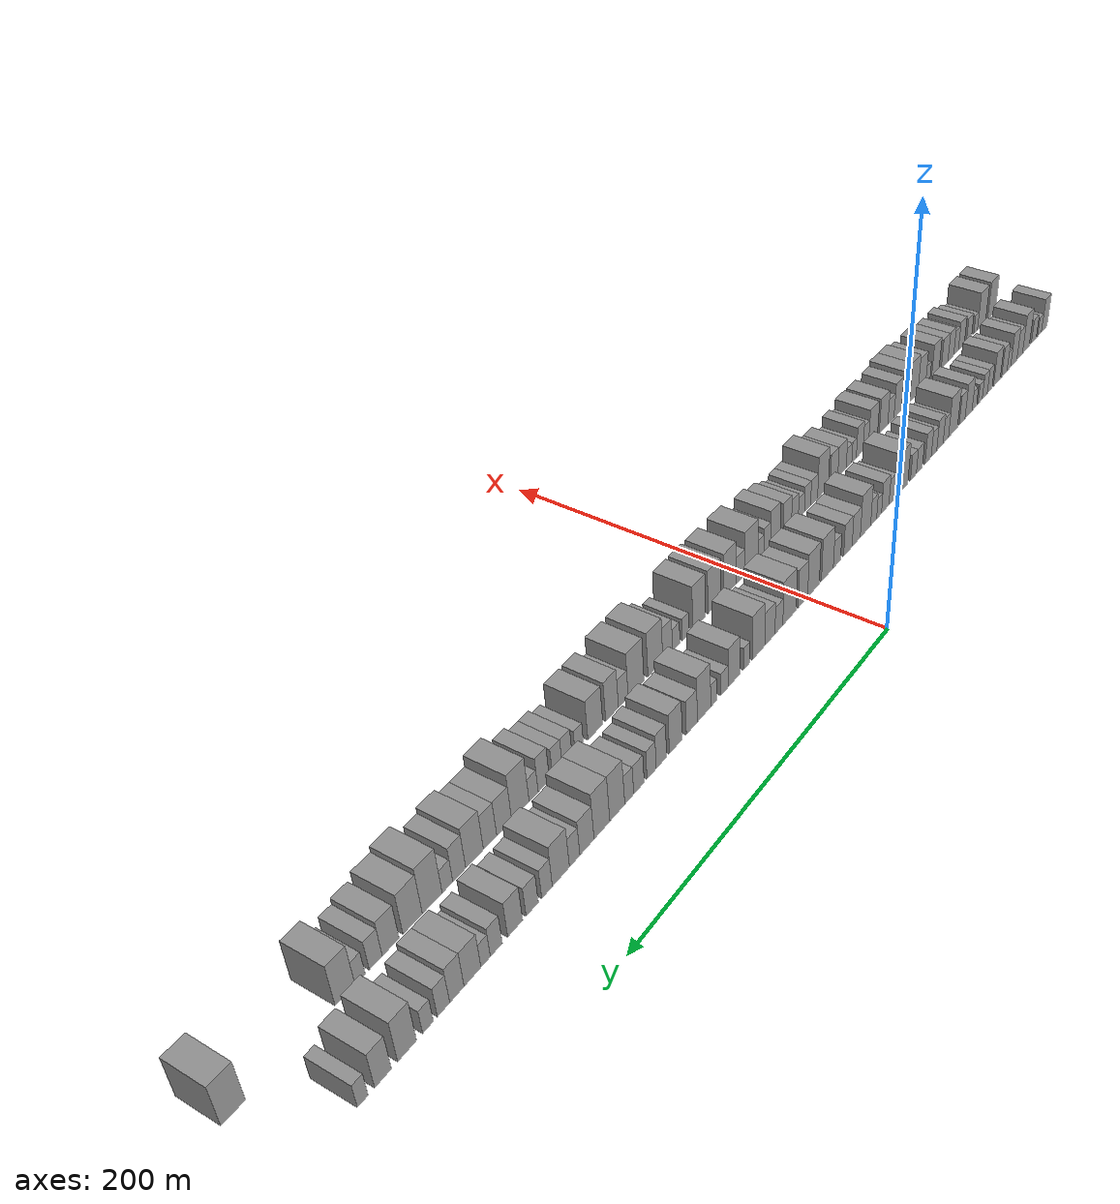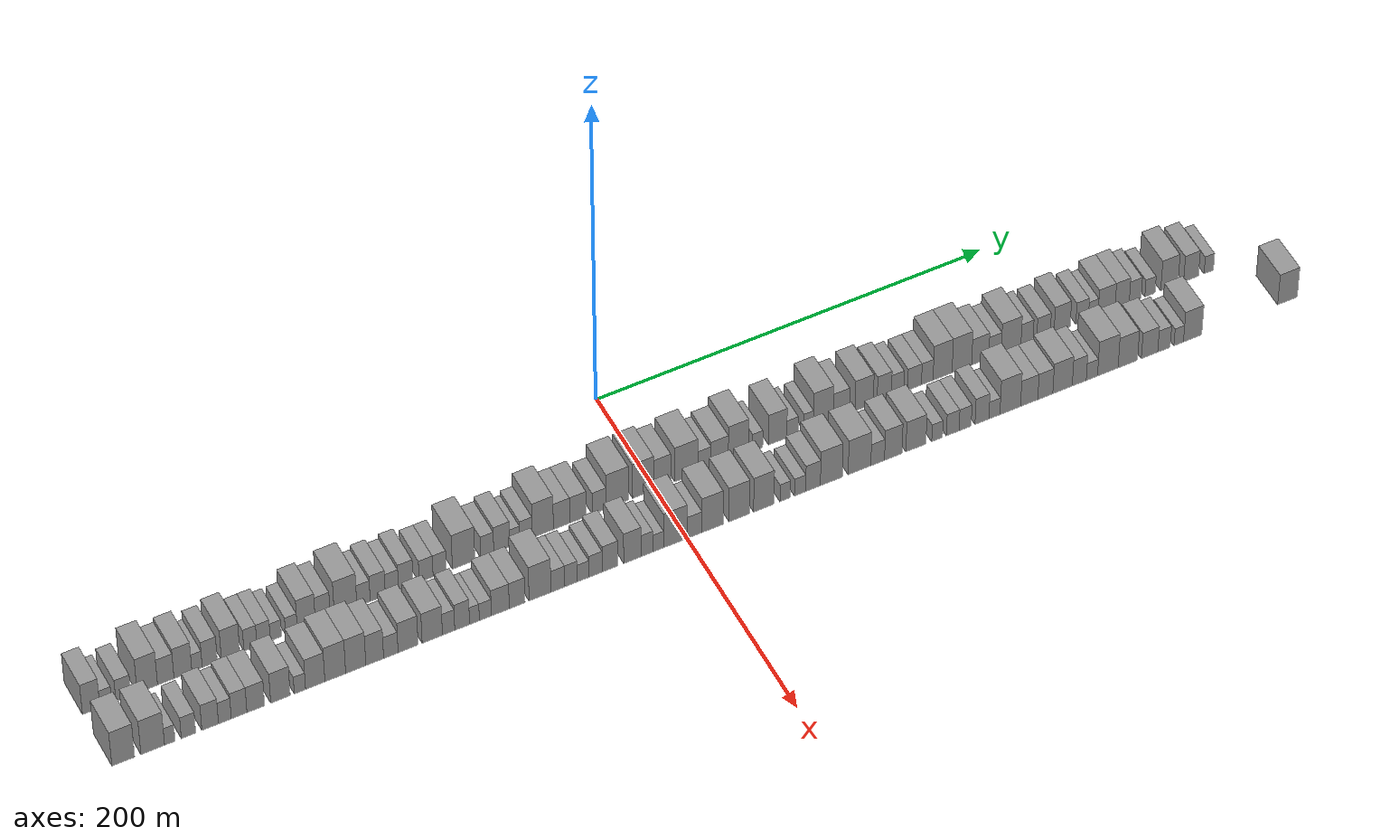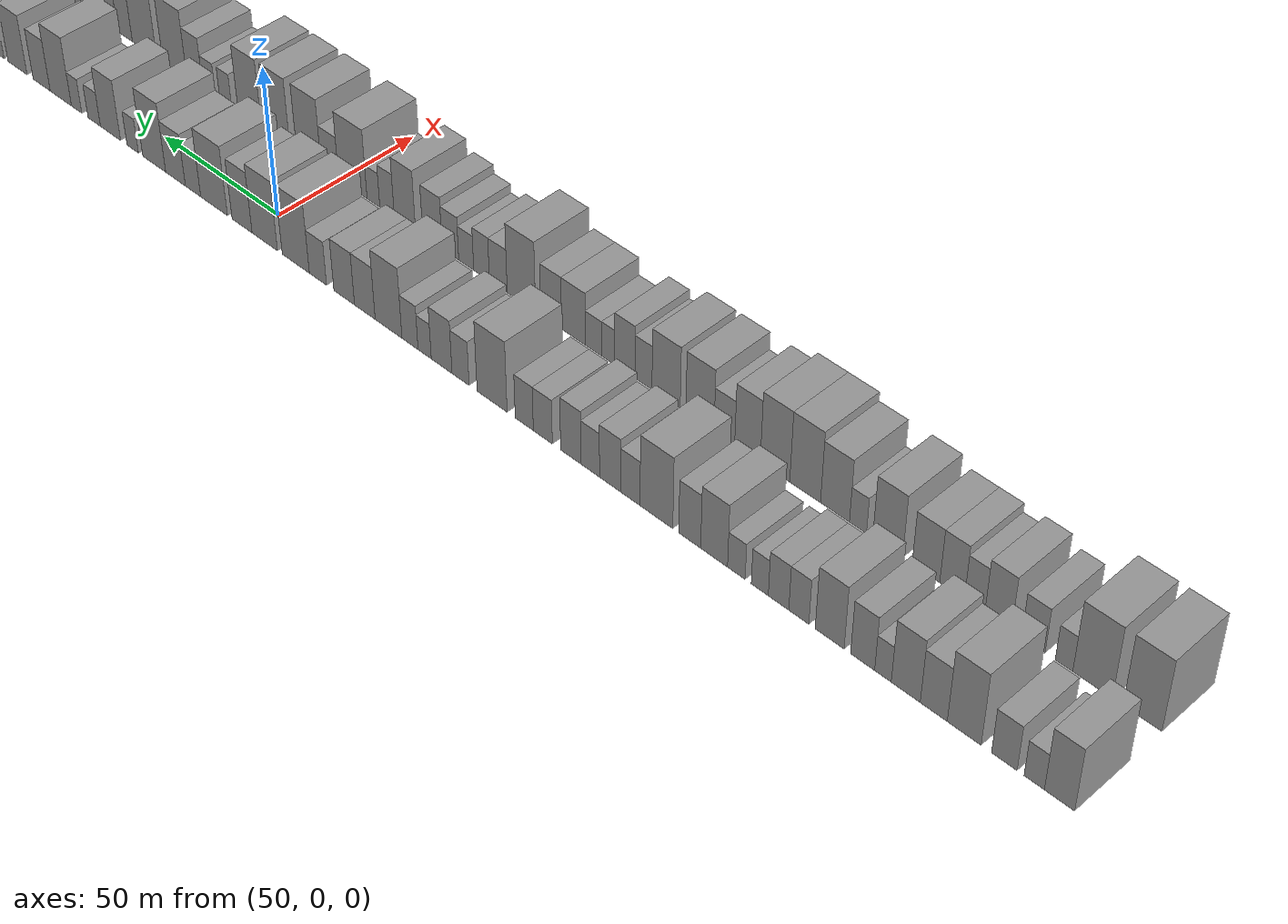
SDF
<sdf version="1.6">
 <world name="default">
  <scene>
   <sky><clouds><speed>12</speed></clouds></sky>
   <ambient>0.4 0.4 0.4 1</ambient>
   <background>0.7 0.7 0.7 1</background>
   <shadows>1</shadows>
  </scene>
  <gravity>0 0 -9.8066</gravity>
  <magnetic_field>6e-06 2.3e-05 -4.2e-05</magnetic_field>
  <physics default="0" name="default_physics" type="ode">
   <ode>
    <solver>
     <type>quick</type>
     <iters>10</iters>
     <sor>1.0</sor>
     <use_dynamic_moi_rescaling>0</use_dynamic_moi_rescaling>
    </solver>
    <constraints>
     <cfm>0</cfm>
     <erp>0.2</erp>
     <contact_max_correcting_vel>100</contact_max_correcting_vel>
     <contact_surface_layer>0.001</contact_surface_layer>
    </constraints>
   </ode>
   <max_step_size>0.004</max_step_size>
   <real_time_factor>1</real_time_factor>
   <real_time_update_rate>250</real_time_update_rate>
  </physics>
  <light name="sun" type="directional">
   <pose>0 0 10 0 0 0</pose>
   <diffuse>0.8 0.8 0.8 1</diffuse>
   <specular>0.2 0.2 0.2 1</specular>
   <attenuation>
    <range>1000</range>
    <constant>0.9</constant>
    <linear>0.01</linear>
    <quadratic>0.001</quadratic>
   </attenuation>
   <direction>-0.5 0.1 -0.9</direction>
  </light>
  <model name="building_1">
   <static>1</static>
   <pose>50.0000 -279.7703 0 0.000000 0.000000 0.000000</pose>
   <link name="link">
    <pose>0 0 10.50 0 0 0</pose>
    <collision name="collision"><geometry><box><size>20.0000 8.4593 21.0000</size></box></geometry></collision>
    <visual name="visual">
     <cast_shadows>0</cast_shadows>
     <geometry><box><size>20.0000 8.4593 21.0000</size></box></geometry>
     <material>
      <script>
       <uri>model://grey_wall/materials/scripts</uri>
       <uri>model://grey_wall/materials/textures</uri>
       <name>vrc/grey_wall</name>
      </script>
     </material>
    </visual>
   </link>
  </model>
  <model name="building_2">
   <static>1</static>
   <pose>50.0000 -272.6795 0 0.000000 0.000000 0.000000</pose>
   <link name="link">
    <pose>0 0 6.00 0 0 0</pose>
    <collision name="collision"><geometry><box><size>20.0000 5.7224 12.0000</size></box></geometry></collision>
    <visual name="visual">
     <cast_shadows>0</cast_shadows>
     <geometry><box><size>20.0000 5.7224 12.0000</size></box></geometry>
     <material>
      <script>
       <uri>model://grey_wall/materials/scripts</uri>
       <uri>model://grey_wall/materials/textures</uri>
       <name>vrc/grey_wall</name>
      </script>
     </material>
    </visual>
   </link>
  </model>
  <model name="building_3">
   <static>1</static>
   <pose>50.0000 -264.1542 0 0.000000 0.000000 0.000000</pose>
   <link name="link">
    <pose>0 0 7.50 0 0 0</pose>
    <collision name="collision"><geometry><box><size>20.0000 7.3282 15.0000</size></box></geometry></collision>
    <visual name="visual">
     <cast_shadows>0</cast_shadows>
     <geometry><box><size>20.0000 7.3282 15.0000</size></box></geometry>
     <material>
      <script>
       <uri>model://grey_wall/materials/scripts</uri>
       <uri>model://grey_wall/materials/textures</uri>
       <name>vrc/grey_wall</name>
      </script>
     </material>
    </visual>
   </link>
  </model>
  <model name="building_4">
   <static>1</static>
   <pose>50.0000 -252.5443 0 0.000000 0.000000 0.000000</pose>
   <link name="link">
    <pose>0 0 12.00 0 0 0</pose>
    <collision name="collision"><geometry><box><size>20.0000 9.8916 24.0000</size></box></geometry></collision>
    <visual name="visual">
     <cast_shadows>0</cast_shadows>
     <geometry><box><size>20.0000 9.8916 24.0000</size></box></geometry>
     <material>
      <script>
       <uri>model://grey_wall/materials/scripts</uri>
       <uri>model://grey_wall/materials/textures</uri>
       <name>vrc/grey_wall</name>
      </script>
     </material>
    </visual>
   </link>
  </model>
  <model name="building_5">
   <static>1</static>
   <pose>50.0000 -243.5871 0 0.000000 0.000000 0.000000</pose>
   <link name="link">
    <pose>0 0 9.00 0 0 0</pose>
    <collision name="collision"><geometry><box><size>20.0000 8.0228 18.0000</size></box></geometry></collision>
    <visual name="visual">
     <cast_shadows>0</cast_shadows>
     <geometry><box><size>20.0000 8.0228 18.0000</size></box></geometry>
     <material>
      <script>
       <uri>model://grey_wall/materials/scripts</uri>
       <uri>model://grey_wall/materials/textures</uri>
       <name>vrc/grey_wall</name>
      </script>
     </material>
    </visual>
   </link>
  </model>
  <model name="building_6">
   <static>1</static>
   <pose>50.0000 -235.2132 0 0.000000 0.000000 0.000000</pose>
   <link name="link">
    <pose>0 0 10.50 0 0 0</pose>
    <collision name="collision"><geometry><box><size>20.0000 8.7249 21.0000</size></box></geometry></collision>
    <visual name="visual">
     <cast_shadows>0</cast_shadows>
     <geometry><box><size>20.0000 8.7249 21.0000</size></box></geometry>
     <material>
      <script>
       <uri>model://grey_wall/materials/scripts</uri>
       <uri>model://grey_wall/materials/textures</uri>
       <name>vrc/grey_wall</name>
      </script>
     </material>
    </visual>
   </link>
  </model>
  <model name="building_7">
   <static>1</static>
   <pose>50.0000 -228.3321 0 0.000000 0.000000 0.000000</pose>
   <link name="link">
    <pose>0 0 6.00 0 0 0</pose>
    <collision name="collision"><geometry><box><size>20.0000 5.0373 12.0000</size></box></geometry></collision>
    <visual name="visual">
     <cast_shadows>0</cast_shadows>
     <geometry><box><size>20.0000 5.0373 12.0000</size></box></geometry>
     <material>
      <script>
       <uri>model://grey_wall/materials/scripts</uri>
       <uri>model://grey_wall/materials/textures</uri>
       <name>vrc/grey_wall</name>
      </script>
     </material>
    </visual>
   </link>
  </model>
  <model name="building_8">
   <static>1</static>
   <pose>50.0000 -222.1160 0 0.000000 0.000000 0.000000</pose>
   <link name="link">
    <pose>0 0 9.00 0 0 0</pose>
    <collision name="collision"><geometry><box><size>20.0000 7.3950 18.0000</size></box></geometry></collision>
    <visual name="visual">
     <cast_shadows>0</cast_shadows>
     <geometry><box><size>20.0000 7.3950 18.0000</size></box></geometry>
     <material>
      <script>
       <uri>model://grey_wall/materials/scripts</uri>
       <uri>model://grey_wall/materials/textures</uri>
       <name>vrc/grey_wall</name>
      </script>
     </material>
    </visual>
   </link>
  </model>
  <model name="building_9">
   <static>1</static>
   <pose>50.0000 -211.9056 0 0.000000 0.000000 0.000000</pose>
   <link name="link">
    <pose>0 0 10.50 0 0 0</pose>
    <collision name="collision"><geometry><box><size>20.0000 9.0258 21.0000</size></box></geometry></collision>
    <visual name="visual">
     <cast_shadows>0</cast_shadows>
     <geometry><box><size>20.0000 9.0258 21.0000</size></box></geometry>
     <material>
      <script>
       <uri>model://grey_wall/materials/scripts</uri>
       <uri>model://grey_wall/materials/textures</uri>
       <name>vrc/grey_wall</name>
      </script>
     </material>
    </visual>
   </link>
  </model>
  <model name="building_10">
   <static>1</static>
   <pose>50.0000 -202.2077 0 0.000000 0.000000 0.000000</pose>
   <link name="link">
    <pose>0 0 7.50 0 0 0</pose>
    <collision name="collision"><geometry><box><size>20.0000 6.3702 15.0000</size></box></geometry></collision>
    <visual name="visual">
     <cast_shadows>0</cast_shadows>
     <geometry><box><size>20.0000 6.3702 15.0000</size></box></geometry>
     <material>
      <script>
       <uri>model://grey_wall/materials/scripts</uri>
       <uri>model://grey_wall/materials/textures</uri>
       <name>vrc/grey_wall</name>
      </script>
     </material>
    </visual>
   </link>
  </model>
  <model name="building_11">
   <static>1</static>
   <pose>50.0000 -195.7344 0 0.000000 0.000000 0.000000</pose>
   <link name="link">
    <pose>0 0 7.50 0 0 0</pose>
    <collision name="collision"><geometry><box><size>20.0000 6.5764 15.0000</size></box></geometry></collision>
    <visual name="visual">
     <cast_shadows>0</cast_shadows>
     <geometry><box><size>20.0000 6.5764 15.0000</size></box></geometry>
     <material>
      <script>
       <uri>model://grey_wall/materials/scripts</uri>
       <uri>model://grey_wall/materials/textures</uri>
       <name>vrc/grey_wall</name>
      </script>
     </material>
    </visual>
   </link>
  </model>
  <model name="building_12">
   <static>1</static>
   <pose>50.0000 -189.6909 0 0.000000 0.000000 0.000000</pose>
   <link name="link">
    <pose>0 0 6.00 0 0 0</pose>
    <collision name="collision"><geometry><box><size>20.0000 5.5105 12.0000</size></box></geometry></collision>
    <visual name="visual">
     <cast_shadows>0</cast_shadows>
     <geometry><box><size>20.0000 5.5105 12.0000</size></box></geometry>
     <material>
      <script>
       <uri>model://grey_wall/materials/scripts</uri>
       <uri>model://grey_wall/materials/textures</uri>
       <name>vrc/grey_wall</name>
      </script>
     </material>
    </visual>
   </link>
  </model>
  <model name="building_13">
   <static>1</static>
   <pose>50.0000 -182.0485 0 0.000000 0.000000 0.000000</pose>
   <link name="link">
    <pose>0 0 6.00 0 0 0</pose>
    <collision name="collision"><geometry><box><size>20.0000 5.7744 12.0000</size></box></geometry></collision>
    <visual name="visual">
     <cast_shadows>0</cast_shadows>
     <geometry><box><size>20.0000 5.7744 12.0000</size></box></geometry>
     <material>
      <script>
       <uri>model://grey_wall/materials/scripts</uri>
       <uri>model://grey_wall/materials/textures</uri>
       <name>vrc/grey_wall</name>
      </script>
     </material>
    </visual>
   </link>
  </model>
  <model name="building_14">
   <static>1</static>
   <pose>50.0000 -174.7064 0 0.000000 0.000000 0.000000</pose>
   <link name="link">
    <pose>0 0 10.50 0 0 0</pose>
    <collision name="collision"><geometry><box><size>20.0000 8.9098 21.0000</size></box></geometry></collision>
    <visual name="visual">
     <cast_shadows>0</cast_shadows>
     <geometry><box><size>20.0000 8.9098 21.0000</size></box></geometry>
     <material>
      <script>
       <uri>model://grey_wall/materials/scripts</uri>
       <uri>model://grey_wall/materials/textures</uri>
       <name>vrc/grey_wall</name>
      </script>
     </material>
    </visual>
   </link>
  </model>
  <model name="building_15">
   <static>1</static>
   <pose>50.0000 -166.5727 0 0.000000 0.000000 0.000000</pose>
   <link name="link">
    <pose>0 0 9.00 0 0 0</pose>
    <collision name="collision"><geometry><box><size>20.0000 7.3575 18.0000</size></box></geometry></collision>
    <visual name="visual">
     <cast_shadows>0</cast_shadows>
     <geometry><box><size>20.0000 7.3575 18.0000</size></box></geometry>
     <material>
      <script>
       <uri>model://grey_wall/materials/scripts</uri>
       <uri>model://grey_wall/materials/textures</uri>
       <name>vrc/grey_wall</name>
      </script>
     </material>
    </visual>
   </link>
  </model>
  <model name="building_16">
   <static>1</static>
   <pose>50.0000 -155.3048 0 0.000000 0.000000 0.000000</pose>
   <link name="link">
    <pose>0 0 12.00 0 0 0</pose>
    <collision name="collision"><geometry><box><size>20.0000 11.1784 24.0000</size></box></geometry></collision>
    <visual name="visual">
     <cast_shadows>0</cast_shadows>
     <geometry><box><size>20.0000 11.1784 24.0000</size></box></geometry>
     <material>
      <script>
       <uri>model://grey_wall/materials/scripts</uri>
       <uri>model://grey_wall/materials/textures</uri>
       <name>vrc/grey_wall</name>
      </script>
     </material>
    </visual>
   </link>
  </model>
  <model name="building_17">
   <static>1</static>
   <pose>50.0000 -146.4196 0 0.000000 0.000000 0.000000</pose>
   <link name="link">
    <pose>0 0 7.50 0 0 0</pose>
    <collision name="collision"><geometry><box><size>20.0000 6.5921 15.0000</size></box></geometry></collision>
    <visual name="visual">
     <cast_shadows>0</cast_shadows>
     <geometry><box><size>20.0000 6.5921 15.0000</size></box></geometry>
     <material>
      <script>
       <uri>model://grey_wall/materials/scripts</uri>
       <uri>model://grey_wall/materials/textures</uri>
       <name>vrc/grey_wall</name>
      </script>
     </material>
    </visual>
   </link>
  </model>
  <model name="building_18">
   <static>1</static>
   <pose>50.0000 -139.3675 0 0.000000 0.000000 0.000000</pose>
   <link name="link">
    <pose>0 0 9.00 0 0 0</pose>
    <collision name="collision"><geometry><box><size>20.0000 7.5121 18.0000</size></box></geometry></collision>
    <visual name="visual">
     <cast_shadows>0</cast_shadows>
     <geometry><box><size>20.0000 7.5121 18.0000</size></box></geometry>
     <material>
      <script>
       <uri>model://grey_wall/materials/scripts</uri>
       <uri>model://grey_wall/materials/textures</uri>
       <name>vrc/grey_wall</name>
      </script>
     </material>
    </visual>
   </link>
  </model>
  <model name="building_19">
   <static>1</static>
   <pose>50.0000 -132.3308 0 0.000000 0.000000 0.000000</pose>
   <link name="link">
    <pose>0 0 7.50 0 0 0</pose>
    <collision name="collision"><geometry><box><size>20.0000 6.5614 15.0000</size></box></geometry></collision>
    <visual name="visual">
     <cast_shadows>0</cast_shadows>
     <geometry><box><size>20.0000 6.5614 15.0000</size></box></geometry>
     <material>
      <script>
       <uri>model://grey_wall/materials/scripts</uri>
       <uri>model://grey_wall/materials/textures</uri>
       <name>vrc/grey_wall</name>
      </script>
     </material>
    </visual>
   </link>
  </model>
  <model name="building_20">
   <static>1</static>
   <pose>50.0000 -125.4148 0 0.000000 0.000000 0.000000</pose>
   <link name="link">
    <pose>0 0 9.00 0 0 0</pose>
    <collision name="collision"><geometry><box><size>20.0000 7.2706 18.0000</size></box></geometry></collision>
    <visual name="visual">
     <cast_shadows>0</cast_shadows>
     <geometry><box><size>20.0000 7.2706 18.0000</size></box></geometry>
     <material>
      <script>
       <uri>model://grey_wall/materials/scripts</uri>
       <uri>model://grey_wall/materials/textures</uri>
       <name>vrc/grey_wall</name>
      </script>
     </material>
    </visual>
   </link>
  </model>
  <model name="building_21">
   <static>1</static>
   <pose>50.0000 -115.3287 0 0.000000 0.000000 0.000000</pose>
   <link name="link">
    <pose>0 0 7.50 0 0 0</pose>
    <collision name="collision"><geometry><box><size>20.0000 6.9017 15.0000</size></box></geometry></collision>
    <visual name="visual">
     <cast_shadows>0</cast_shadows>
     <geometry><box><size>20.0000 6.9017 15.0000</size></box></geometry>
     <material>
      <script>
       <uri>model://grey_wall/materials/scripts</uri>
       <uri>model://grey_wall/materials/textures</uri>
       <name>vrc/grey_wall</name>
      </script>
     </material>
    </visual>
   </link>
  </model>
  <model name="building_22">
   <static>1</static>
   <pose>50.0000 -108.5586 0 0.000000 0.000000 0.000000</pose>
   <link name="link">
    <pose>0 0 7.50 0 0 0</pose>
    <collision name="collision"><geometry><box><size>20.0000 6.6385 15.0000</size></box></geometry></collision>
    <visual name="visual">
     <cast_shadows>0</cast_shadows>
     <geometry><box><size>20.0000 6.6385 15.0000</size></box></geometry>
     <material>
      <script>
       <uri>model://grey_wall/materials/scripts</uri>
       <uri>model://grey_wall/materials/textures</uri>
       <name>vrc/grey_wall</name>
      </script>
     </material>
    </visual>
   </link>
  </model>
  <model name="building_23">
   <static>1</static>
   <pose>50.0000 -96.6324 0 0.000000 0.000000 0.000000</pose>
   <link name="link">
    <pose>0 0 12.00 0 0 0</pose>
    <collision name="collision"><geometry><box><size>20.0000 11.2139 24.0000</size></box></geometry></collision>
    <visual name="visual">
     <cast_shadows>0</cast_shadows>
     <geometry><box><size>20.0000 11.2139 24.0000</size></box></geometry>
     <material>
      <script>
       <uri>model://grey_wall/materials/scripts</uri>
       <uri>model://grey_wall/materials/textures</uri>
       <name>vrc/grey_wall</name>
      </script>
     </material>
    </visual>
   </link>
  </model>
  <model name="building_24">
   <static>1</static>
   <pose>50.0000 -84.7754 0 0.000000 0.000000 0.000000</pose>
   <link name="link">
    <pose>0 0 7.50 0 0 0</pose>
    <collision name="collision"><geometry><box><size>20.0000 6.5001 15.0000</size></box></geometry></collision>
    <visual name="visual">
     <cast_shadows>0</cast_shadows>
     <geometry><box><size>20.0000 6.5001 15.0000</size></box></geometry>
     <material>
      <script>
       <uri>model://grey_wall/materials/scripts</uri>
       <uri>model://grey_wall/materials/textures</uri>
       <name>vrc/grey_wall</name>
      </script>
     </material>
    </visual>
   </link>
  </model>
  <model name="building_25">
   <static>1</static>
   <pose>50.0000 -77.5405 0 0.000000 0.000000 0.000000</pose>
   <link name="link">
    <pose>0 0 9.00 0 0 0</pose>
    <collision name="collision"><geometry><box><size>20.0000 7.9698 18.0000</size></box></geometry></collision>
    <visual name="visual">
     <cast_shadows>0</cast_shadows>
     <geometry><box><size>20.0000 7.9698 18.0000</size></box></geometry>
     <material>
      <script>
       <uri>model://grey_wall/materials/scripts</uri>
       <uri>model://grey_wall/materials/textures</uri>
       <name>vrc/grey_wall</name>
      </script>
     </material>
    </visual>
   </link>
  </model>
  <model name="building_26">
   <static>1</static>
   <pose>50.0000 -70.9993 0 0.000000 0.000000 0.000000</pose>
   <link name="link">
    <pose>0 0 6.00 0 0 0</pose>
    <collision name="collision"><geometry><box><size>20.0000 5.1126 12.0000</size></box></geometry></collision>
    <visual name="visual">
     <cast_shadows>0</cast_shadows>
     <geometry><box><size>20.0000 5.1126 12.0000</size></box></geometry>
     <material>
      <script>
       <uri>model://grey_wall/materials/scripts</uri>
       <uri>model://grey_wall/materials/textures</uri>
       <name>vrc/grey_wall</name>
      </script>
     </material>
    </visual>
   </link>
  </model>
  <model name="building_27">
   <static>1</static>
   <pose>50.0000 -65.3010 0 0.000000 0.000000 0.000000</pose>
   <link name="link">
    <pose>0 0 7.50 0 0 0</pose>
    <collision name="collision"><geometry><box><size>20.0000 6.2841 15.0000</size></box></geometry></collision>
    <visual name="visual">
     <cast_shadows>0</cast_shadows>
     <geometry><box><size>20.0000 6.2841 15.0000</size></box></geometry>
     <material>
      <script>
       <uri>model://grey_wall/materials/scripts</uri>
       <uri>model://grey_wall/materials/textures</uri>
       <name>vrc/grey_wall</name>
      </script>
     </material>
    </visual>
   </link>
  </model>
  <model name="building_28">
   <static>1</static>
   <pose>50.0000 -56.8508 0 0.000000 0.000000 0.000000</pose>
   <link name="link">
    <pose>0 0 12.00 0 0 0</pose>
    <collision name="collision"><geometry><box><size>20.0000 10.6163 24.0000</size></box></geometry></collision>
    <visual name="visual">
     <cast_shadows>0</cast_shadows>
     <geometry><box><size>20.0000 10.6163 24.0000</size></box></geometry>
     <material>
      <script>
       <uri>model://grey_wall/materials/scripts</uri>
       <uri>model://grey_wall/materials/textures</uri>
       <name>vrc/grey_wall</name>
      </script>
     </material>
    </visual>
   </link>
  </model>
  <model name="building_29">
   <static>1</static>
   <pose>50.0000 -47.4027 0 0.000000 0.000000 0.000000</pose>
   <link name="link">
    <pose>0 0 9.00 0 0 0</pose>
    <collision name="collision"><geometry><box><size>20.0000 8.2799 18.0000</size></box></geometry></collision>
    <visual name="visual">
     <cast_shadows>0</cast_shadows>
     <geometry><box><size>20.0000 8.2799 18.0000</size></box></geometry>
     <material>
      <script>
       <uri>model://grey_wall/materials/scripts</uri>
       <uri>model://grey_wall/materials/textures</uri>
       <name>vrc/grey_wall</name>
      </script>
     </material>
    </visual>
   </link>
  </model>
  <model name="building_30">
   <static>1</static>
   <pose>50.0000 -39.0832 0 0.000000 0.000000 0.000000</pose>
   <link name="link">
    <pose>0 0 9.00 0 0 0</pose>
    <collision name="collision"><geometry><box><size>20.0000 8.3590 18.0000</size></box></geometry></collision>
    <visual name="visual">
     <cast_shadows>0</cast_shadows>
     <geometry><box><size>20.0000 8.3590 18.0000</size></box></geometry>
     <material>
      <script>
       <uri>model://grey_wall/materials/scripts</uri>
       <uri>model://grey_wall/materials/textures</uri>
       <name>vrc/grey_wall</name>
      </script>
     </material>
    </visual>
   </link>
  </model>
  <model name="building_31">
   <static>1</static>
   <pose>50.0000 -28.3617 0 0.000000 0.000000 0.000000</pose>
   <link name="link">
    <pose>0 0 7.50 0 0 0</pose>
    <collision name="collision"><geometry><box><size>20.0000 7.0841 15.0000</size></box></geometry></collision>
    <visual name="visual">
     <cast_shadows>0</cast_shadows>
     <geometry><box><size>20.0000 7.0841 15.0000</size></box></geometry>
     <material>
      <script>
       <uri>model://grey_wall/materials/scripts</uri>
       <uri>model://grey_wall/materials/textures</uri>
       <name>vrc/grey_wall</name>
      </script>
     </material>
    </visual>
   </link>
  </model>
  <model name="building_32">
   <static>1</static>
   <pose>50.0000 -19.1570 0 0.000000 0.000000 0.000000</pose>
   <link name="link">
    <pose>0 0 12.00 0 0 0</pose>
    <collision name="collision"><geometry><box><size>20.0000 11.3253 24.0000</size></box></geometry></collision>
    <visual name="visual">
     <cast_shadows>0</cast_shadows>
     <geometry><box><size>20.0000 11.3253 24.0000</size></box></geometry>
     <material>
      <script>
       <uri>model://grey_wall/materials/scripts</uri>
       <uri>model://grey_wall/materials/textures</uri>
       <name>vrc/grey_wall</name>
      </script>
     </material>
    </visual>
   </link>
  </model>
  <model name="building_33">
   <static>1</static>
   <pose>50.0000 -6.0916 0 0.000000 0.000000 0.000000</pose>
   <link name="link">
    <pose>0 0 12.00 0 0 0</pose>
    <collision name="collision"><geometry><box><size>20.0000 10.8056 24.0000</size></box></geometry></collision>
    <visual name="visual">
     <cast_shadows>0</cast_shadows>
     <geometry><box><size>20.0000 10.8056 24.0000</size></box></geometry>
     <material>
      <script>
       <uri>model://grey_wall/materials/scripts</uri>
       <uri>model://grey_wall/materials/textures</uri>
       <name>vrc/grey_wall</name>
      </script>
     </material>
    </visual>
   </link>
  </model>
  <model name="building_34">
   <static>1</static>
   <pose>50.0000 3.6249 0 0.000000 0.000000 0.000000</pose>
   <link name="link">
    <pose>0 0 10.50 0 0 0</pose>
    <collision name="collision"><geometry><box><size>20.0000 8.6273 21.0000</size></box></geometry></collision>
    <visual name="visual">
     <cast_shadows>0</cast_shadows>
     <geometry><box><size>20.0000 8.6273 21.0000</size></box></geometry>
     <material>
      <script>
       <uri>model://grey_wall/materials/scripts</uri>
       <uri>model://grey_wall/materials/textures</uri>
       <name>vrc/grey_wall</name>
      </script>
     </material>
    </visual>
   </link>
  </model>
  <model name="building_35">
   <static>1</static>
   <pose>50.0000 15.7921 0 0.000000 0.000000 0.000000</pose>
   <link name="link">
    <pose>0 0 12.00 0 0 0</pose>
    <collision name="collision"><geometry><box><size>20.0000 11.7071 24.0000</size></box></geometry></collision>
    <visual name="visual">
     <cast_shadows>0</cast_shadows>
     <geometry><box><size>20.0000 11.7071 24.0000</size></box></geometry>
     <material>
      <script>
       <uri>model://grey_wall/materials/scripts</uri>
       <uri>model://grey_wall/materials/textures</uri>
       <name>vrc/grey_wall</name>
      </script>
     </material>
    </visual>
   </link>
  </model>
  <model name="building_36">
   <static>1</static>
   <pose>50.0000 25.0424 0 0.000000 0.000000 0.000000</pose>
   <link name="link">
    <pose>0 0 7.50 0 0 0</pose>
    <collision name="collision"><geometry><box><size>20.0000 6.7934 15.0000</size></box></geometry></collision>
    <visual name="visual">
     <cast_shadows>0</cast_shadows>
     <geometry><box><size>20.0000 6.7934 15.0000</size></box></geometry>
     <material>
      <script>
       <uri>model://grey_wall/materials/scripts</uri>
       <uri>model://grey_wall/materials/textures</uri>
       <name>vrc/grey_wall</name>
      </script>
     </material>
    </visual>
   </link>
  </model>
  <model name="building_37">
   <static>1</static>
   <pose>50.0000 32.8553 0 0.000000 0.000000 0.000000</pose>
   <link name="link">
    <pose>0 0 9.00 0 0 0</pose>
    <collision name="collision"><geometry><box><size>20.0000 8.8324 18.0000</size></box></geometry></collision>
    <visual name="visual">
     <cast_shadows>0</cast_shadows>
     <geometry><box><size>20.0000 8.8324 18.0000</size></box></geometry>
     <material>
      <script>
       <uri>model://grey_wall/materials/scripts</uri>
       <uri>model://grey_wall/materials/textures</uri>
       <name>vrc/grey_wall</name>
      </script>
     </material>
    </visual>
   </link>
  </model>
  <model name="building_38">
   <static>1</static>
   <pose>50.0000 42.4731 0 0.000000 0.000000 0.000000</pose>
   <link name="link">
    <pose>0 0 12.00 0 0 0</pose>
    <collision name="collision"><geometry><box><size>20.0000 10.4032 24.0000</size></box></geometry></collision>
    <visual name="visual">
     <cast_shadows>0</cast_shadows>
     <geometry><box><size>20.0000 10.4032 24.0000</size></box></geometry>
     <material>
      <script>
       <uri>model://grey_wall/materials/scripts</uri>
       <uri>model://grey_wall/materials/textures</uri>
       <name>vrc/grey_wall</name>
      </script>
     </material>
    </visual>
   </link>
  </model>
  <model name="building_39">
   <static>1</static>
   <pose>50.0000 52.2964 0 0.000000 0.000000 0.000000</pose>
   <link name="link">
    <pose>0 0 6.00 0 0 0</pose>
    <collision name="collision"><geometry><box><size>20.0000 5.2434 12.0000</size></box></geometry></collision>
    <visual name="visual">
     <cast_shadows>0</cast_shadows>
     <geometry><box><size>20.0000 5.2434 12.0000</size></box></geometry>
     <material>
      <script>
       <uri>model://grey_wall/materials/scripts</uri>
       <uri>model://grey_wall/materials/textures</uri>
       <name>vrc/grey_wall</name>
      </script>
     </material>
    </visual>
   </link>
  </model>
  <model name="building_40">
   <static>1</static>
   <pose>50.0000 62.6098 0 0.000000 0.000000 0.000000</pose>
   <link name="link">
    <pose>0 0 10.50 0 0 0</pose>
    <collision name="collision"><geometry><box><size>20.0000 9.3833 21.0000</size></box></geometry></collision>
    <visual name="visual">
     <cast_shadows>0</cast_shadows>
     <geometry><box><size>20.0000 9.3833 21.0000</size></box></geometry>
     <material>
      <script>
       <uri>model://grey_wall/materials/scripts</uri>
       <uri>model://grey_wall/materials/textures</uri>
       <name>vrc/grey_wall</name>
      </script>
     </material>
    </visual>
   </link>
  </model>
  <model name="building_41">
   <static>1</static>
   <pose>50.0000 70.1989 0 0.000000 0.000000 0.000000</pose>
   <link name="link">
    <pose>0 0 6.00 0 0 0</pose>
    <collision name="collision"><geometry><box><size>20.0000 5.7951 12.0000</size></box></geometry></collision>
    <visual name="visual">
     <cast_shadows>0</cast_shadows>
     <geometry><box><size>20.0000 5.7951 12.0000</size></box></geometry>
     <material>
      <script>
       <uri>model://grey_wall/materials/scripts</uri>
       <uri>model://grey_wall/materials/textures</uri>
       <name>vrc/grey_wall</name>
      </script>
     </material>
    </visual>
   </link>
  </model>
  <model name="building_42">
   <static>1</static>
   <pose>50.0000 78.5643 0 0.000000 0.000000 0.000000</pose>
   <link name="link">
    <pose>0 0 6.00 0 0 0</pose>
    <collision name="collision"><geometry><box><size>20.0000 4.9357 12.0000</size></box></geometry></collision>
    <visual name="visual">
     <cast_shadows>0</cast_shadows>
     <geometry><box><size>20.0000 4.9357 12.0000</size></box></geometry>
     <material>
      <script>
       <uri>model://grey_wall/materials/scripts</uri>
       <uri>model://grey_wall/materials/textures</uri>
       <name>vrc/grey_wall</name>
      </script>
     </material>
    </visual>
   </link>
  </model>
  <model name="building_43">
   <static>1</static>
   <pose>50.0000 86.1423 0 0.000000 0.000000 0.000000</pose>
   <link name="link">
    <pose>0 0 12.00 0 0 0</pose>
    <collision name="collision"><geometry><box><size>20.0000 10.2202 24.0000</size></box></geometry></collision>
    <visual name="visual">
     <cast_shadows>0</cast_shadows>
     <geometry><box><size>20.0000 10.2202 24.0000</size></box></geometry>
     <material>
      <script>
       <uri>model://grey_wall/materials/scripts</uri>
       <uri>model://grey_wall/materials/textures</uri>
       <name>vrc/grey_wall</name>
      </script>
     </material>
    </visual>
   </link>
  </model>
  <model name="building_44">
   <static>1</static>
   <pose>50.0000 95.3899 0 0.000000 0.000000 0.000000</pose>
   <link name="link">
    <pose>0 0 9.00 0 0 0</pose>
    <collision name="collision"><geometry><box><size>20.0000 8.2749 18.0000</size></box></geometry></collision>
    <visual name="visual">
     <cast_shadows>0</cast_shadows>
     <geometry><box><size>20.0000 8.2749 18.0000</size></box></geometry>
     <material>
      <script>
       <uri>model://grey_wall/materials/scripts</uri>
       <uri>model://grey_wall/materials/textures</uri>
       <name>vrc/grey_wall</name>
      </script>
     </material>
    </visual>
   </link>
  </model>
  <model name="building_45">
   <static>1</static>
   <pose>50.0000 107.2304 0 0.000000 0.000000 0.000000</pose>
   <link name="link">
    <pose>0 0 10.50 0 0 0</pose>
    <collision name="collision"><geometry><box><size>20.0000 9.4060 21.0000</size></box></geometry></collision>
    <visual name="visual">
     <cast_shadows>0</cast_shadows>
     <geometry><box><size>20.0000 9.4060 21.0000</size></box></geometry>
     <material>
      <script>
       <uri>model://grey_wall/materials/scripts</uri>
       <uri>model://grey_wall/materials/textures</uri>
       <name>vrc/grey_wall</name>
      </script>
     </material>
    </visual>
   </link>
  </model>
  <model name="building_46">
   <static>1</static>
   <pose>50.0000 117.6209 0 0.000000 0.000000 0.000000</pose>
   <link name="link">
    <pose>0 0 9.00 0 0 0</pose>
    <collision name="collision"><geometry><box><size>20.0000 7.3749 18.0000</size></box></geometry></collision>
    <visual name="visual">
     <cast_shadows>0</cast_shadows>
     <geometry><box><size>20.0000 7.3749 18.0000</size></box></geometry>
     <material>
      <script>
       <uri>model://grey_wall/materials/scripts</uri>
       <uri>model://grey_wall/materials/textures</uri>
       <name>vrc/grey_wall</name>
      </script>
     </material>
    </visual>
   </link>
  </model>
  <model name="building_47">
   <static>1</static>
   <pose>50.0000 124.5453 0 0.000000 0.000000 0.000000</pose>
   <link name="link">
    <pose>0 0 7.50 0 0 0</pose>
    <collision name="collision"><geometry><box><size>20.0000 6.4739 15.0000</size></box></geometry></collision>
    <visual name="visual">
     <cast_shadows>0</cast_shadows>
     <geometry><box><size>20.0000 6.4739 15.0000</size></box></geometry>
     <material>
      <script>
       <uri>model://grey_wall/materials/scripts</uri>
       <uri>model://grey_wall/materials/textures</uri>
       <name>vrc/grey_wall</name>
      </script>
     </material>
    </visual>
   </link>
  </model>
  <model name="building_48">
   <static>1</static>
   <pose>50.0000 133.3689 0 0.000000 0.000000 0.000000</pose>
   <link name="link">
    <pose>0 0 7.50 0 0 0</pose>
    <collision name="collision"><geometry><box><size>20.0000 7.1733 15.0000</size></box></geometry></collision>
    <visual name="visual">
     <cast_shadows>0</cast_shadows>
     <geometry><box><size>20.0000 7.1733 15.0000</size></box></geometry>
     <material>
      <script>
       <uri>model://grey_wall/materials/scripts</uri>
       <uri>model://grey_wall/materials/textures</uri>
       <name>vrc/grey_wall</name>
      </script>
     </material>
    </visual>
   </link>
  </model>
  <model name="building_49">
   <static>1</static>
   <pose>50.0000 139.9846 0 0.000000 0.000000 0.000000</pose>
   <link name="link">
    <pose>0 0 7.50 0 0 0</pose>
    <collision name="collision"><geometry><box><size>20.0000 6.0581 15.0000</size></box></geometry></collision>
    <visual name="visual">
     <cast_shadows>0</cast_shadows>
     <geometry><box><size>20.0000 6.0581 15.0000</size></box></geometry>
     <material>
      <script>
       <uri>model://grey_wall/materials/scripts</uri>
       <uri>model://grey_wall/materials/textures</uri>
       <name>vrc/grey_wall</name>
      </script>
     </material>
    </visual>
   </link>
  </model>
  <model name="building_50">
   <static>1</static>
   <pose>50.0000 147.9668 0 0.000000 0.000000 0.000000</pose>
   <link name="link">
    <pose>0 0 12.00 0 0 0</pose>
    <collision name="collision"><geometry><box><size>20.0000 9.9063 24.0000</size></box></geometry></collision>
    <visual name="visual">
     <cast_shadows>0</cast_shadows>
     <geometry><box><size>20.0000 9.9063 24.0000</size></box></geometry>
     <material>
      <script>
       <uri>model://grey_wall/materials/scripts</uri>
       <uri>model://grey_wall/materials/textures</uri>
       <name>vrc/grey_wall</name>
      </script>
     </material>
    </visual>
   </link>
  </model>
  <model name="building_51">
   <static>1</static>
   <pose>50.0000 158.0264 0 0.000000 0.000000 0.000000</pose>
   <link name="link">
    <pose>0 0 12.00 0 0 0</pose>
    <collision name="collision"><geometry><box><size>20.0000 10.2129 24.0000</size></box></geometry></collision>
    <visual name="visual">
     <cast_shadows>0</cast_shadows>
     <geometry><box><size>20.0000 10.2129 24.0000</size></box></geometry>
     <material>
      <script>
       <uri>model://grey_wall/materials/scripts</uri>
       <uri>model://grey_wall/materials/textures</uri>
       <name>vrc/grey_wall</name>
      </script>
     </material>
    </visual>
   </link>
  </model>
  <model name="building_52">
   <static>1</static>
   <pose>50.0000 167.6139 0 0.000000 0.000000 0.000000</pose>
   <link name="link">
    <pose>0 0 9.00 0 0 0</pose>
    <collision name="collision"><geometry><box><size>20.0000 8.9620 18.0000</size></box></geometry></collision>
    <visual name="visual">
     <cast_shadows>0</cast_shadows>
     <geometry><box><size>20.0000 8.9620 18.0000</size></box></geometry>
     <material>
      <script>
       <uri>model://grey_wall/materials/scripts</uri>
       <uri>model://grey_wall/materials/textures</uri>
       <name>vrc/grey_wall</name>
      </script>
     </material>
    </visual>
   </link>
  </model>
  <model name="building_53">
   <static>1</static>
   <pose>50.0000 175.3463 0 0.000000 0.000000 0.000000</pose>
   <link name="link">
    <pose>0 0 7.50 0 0 0</pose>
    <collision name="collision"><geometry><box><size>20.0000 6.5030 15.0000</size></box></geometry></collision>
    <visual name="visual">
     <cast_shadows>0</cast_shadows>
     <geometry><box><size>20.0000 6.5030 15.0000</size></box></geometry>
     <material>
      <script>
       <uri>model://grey_wall/materials/scripts</uri>
       <uri>model://grey_wall/materials/textures</uri>
       <name>vrc/grey_wall</name>
      </script>
     </material>
    </visual>
   </link>
  </model>
  <model name="building_54">
   <static>1</static>
   <pose>50.0000 183.7897 0 0.000000 0.000000 0.000000</pose>
   <link name="link">
    <pose>0 0 10.50 0 0 0</pose>
    <collision name="collision"><geometry><box><size>20.0000 10.3837 21.0000</size></box></geometry></collision>
    <visual name="visual">
     <cast_shadows>0</cast_shadows>
     <geometry><box><size>20.0000 10.3837 21.0000</size></box></geometry>
     <material>
      <script>
       <uri>model://grey_wall/materials/scripts</uri>
       <uri>model://grey_wall/materials/textures</uri>
       <name>vrc/grey_wall</name>
      </script>
     </material>
    </visual>
   </link>
  </model>
  <model name="building_55">
   <static>1</static>
   <pose>50.0000 192.1452 0 0.000000 0.000000 0.000000</pose>
   <link name="link">
    <pose>0 0 7.50 0 0 0</pose>
    <collision name="collision"><geometry><box><size>20.0000 6.3272 15.0000</size></box></geometry></collision>
    <visual name="visual">
     <cast_shadows>0</cast_shadows>
     <geometry><box><size>20.0000 6.3272 15.0000</size></box></geometry>
     <material>
      <script>
       <uri>model://grey_wall/materials/scripts</uri>
       <uri>model://grey_wall/materials/textures</uri>
       <name>vrc/grey_wall</name>
      </script>
     </material>
    </visual>
   </link>
  </model>
  <model name="building_56">
   <static>1</static>
   <pose>50.0000 200.8737 0 0.000000 0.000000 0.000000</pose>
   <link name="link">
    <pose>0 0 7.50 0 0 0</pose>
    <collision name="collision"><geometry><box><size>20.0000 7.1298 15.0000</size></box></geometry></collision>
    <visual name="visual">
     <cast_shadows>0</cast_shadows>
     <geometry><box><size>20.0000 7.1298 15.0000</size></box></geometry>
     <material>
      <script>
       <uri>model://grey_wall/materials/scripts</uri>
       <uri>model://grey_wall/materials/textures</uri>
       <name>vrc/grey_wall</name>
      </script>
     </material>
    </visual>
   </link>
  </model>
  <model name="building_57">
   <static>1</static>
   <pose>50.0000 210.6754 0 0.000000 0.000000 0.000000</pose>
   <link name="link">
    <pose>0 0 9.00 0 0 0</pose>
    <collision name="collision"><geometry><box><size>20.0000 8.4736 18.0000</size></box></geometry></collision>
    <visual name="visual">
     <cast_shadows>0</cast_shadows>
     <geometry><box><size>20.0000 8.4736 18.0000</size></box></geometry>
     <material>
      <script>
       <uri>model://grey_wall/materials/scripts</uri>
       <uri>model://grey_wall/materials/textures</uri>
       <name>vrc/grey_wall</name>
      </script>
     </material>
    </visual>
   </link>
  </model>
  <model name="building_58">
   <static>1</static>
   <pose>50.0000 221.2127 0 0.000000 0.000000 0.000000</pose>
   <link name="link">
    <pose>0 0 7.50 0 0 0</pose>
    <collision name="collision"><geometry><box><size>20.0000 6.6009 15.0000</size></box></geometry></collision>
    <visual name="visual">
     <cast_shadows>0</cast_shadows>
     <geometry><box><size>20.0000 6.6009 15.0000</size></box></geometry>
     <material>
      <script>
       <uri>model://grey_wall/materials/scripts</uri>
       <uri>model://grey_wall/materials/textures</uri>
       <name>vrc/grey_wall</name>
      </script>
     </material>
    </visual>
   </link>
  </model>
  <model name="building_59">
   <static>1</static>
   <pose>50.0000 227.0809 0 0.000000 0.000000 0.000000</pose>
   <link name="link">
    <pose>0 0 6.00 0 0 0</pose>
    <collision name="collision"><geometry><box><size>20.0000 5.1356 12.0000</size></box></geometry></collision>
    <visual name="visual">
     <cast_shadows>0</cast_shadows>
     <geometry><box><size>20.0000 5.1356 12.0000</size></box></geometry>
     <material>
      <script>
       <uri>model://grey_wall/materials/scripts</uri>
       <uri>model://grey_wall/materials/textures</uri>
       <name>vrc/grey_wall</name>
      </script>
     </material>
    </visual>
   </link>
  </model>
  <model name="building_60">
   <static>1</static>
   <pose>50.0000 234.1412 0 0.000000 0.000000 0.000000</pose>
   <link name="link">
    <pose>0 0 9.00 0 0 0</pose>
    <collision name="collision"><geometry><box><size>20.0000 8.9851 18.0000</size></box></geometry></collision>
    <visual name="visual">
     <cast_shadows>0</cast_shadows>
     <geometry><box><size>20.0000 8.9851 18.0000</size></box></geometry>
     <material>
      <script>
       <uri>model://grey_wall/materials/scripts</uri>
       <uri>model://grey_wall/materials/textures</uri>
       <name>vrc/grey_wall</name>
      </script>
     </material>
    </visual>
   </link>
  </model>
  <model name="building_61">
   <static>1</static>
   <pose>50.0000 242.4022 0 0.000000 0.000000 0.000000</pose>
   <link name="link">
    <pose>0 0 9.00 0 0 0</pose>
    <collision name="collision"><geometry><box><size>20.0000 7.5370 18.0000</size></box></geometry></collision>
    <visual name="visual">
     <cast_shadows>0</cast_shadows>
     <geometry><box><size>20.0000 7.5370 18.0000</size></box></geometry>
     <material>
      <script>
       <uri>model://grey_wall/materials/scripts</uri>
       <uri>model://grey_wall/materials/textures</uri>
       <name>vrc/grey_wall</name>
      </script>
     </material>
    </visual>
   </link>
  </model>
  <model name="building_62">
   <static>1</static>
   <pose>50.0000 249.3360 0 0.000000 0.000000 0.000000</pose>
   <link name="link">
    <pose>0 0 7.50 0 0 0</pose>
    <collision name="collision"><geometry><box><size>20.0000 6.3305 15.0000</size></box></geometry></collision>
    <visual name="visual">
     <cast_shadows>0</cast_shadows>
     <geometry><box><size>20.0000 6.3305 15.0000</size></box></geometry>
     <material>
      <script>
       <uri>model://grey_wall/materials/scripts</uri>
       <uri>model://grey_wall/materials/textures</uri>
       <name>vrc/grey_wall</name>
      </script>
     </material>
    </visual>
   </link>
  </model>
  <model name="building_63">
   <static>1</static>
   <pose>50.0000 257.2135 0 0.000000 0.000000 0.000000</pose>
   <link name="link">
    <pose>0 0 6.00 0 0 0</pose>
    <collision name="collision"><geometry><box><size>20.0000 5.4245 12.0000</size></box></geometry></collision>
    <visual name="visual">
     <cast_shadows>0</cast_shadows>
     <geometry><box><size>20.0000 5.4245 12.0000</size></box></geometry>
     <material>
      <script>
       <uri>model://grey_wall/materials/scripts</uri>
       <uri>model://grey_wall/materials/textures</uri>
       <name>vrc/grey_wall</name>
      </script>
     </material>
    </visual>
   </link>
  </model>
  <model name="building_64">
   <static>1</static>
   <pose>50.0000 267.5240 0 0.000000 0.000000 0.000000</pose>
   <link name="link">
    <pose>0 0 10.50 0 0 0</pose>
    <collision name="collision"><geometry><box><size>20.0000 9.1967 21.0000</size></box></geometry></collision>
    <visual name="visual">
     <cast_shadows>0</cast_shadows>
     <geometry><box><size>20.0000 9.1967 21.0000</size></box></geometry>
     <material>
      <script>
       <uri>model://grey_wall/materials/scripts</uri>
       <uri>model://grey_wall/materials/textures</uri>
       <name>vrc/grey_wall</name>
      </script>
     </material>
    </visual>
   </link>
  </model>
  <model name="building_65">
   <static>1</static>
   <pose>50.0000 279.0898 0 0.000000 0.000000 0.000000</pose>
   <link name="link">
    <pose>0 0 9.00 0 0 0</pose>
    <collision name="collision"><geometry><box><size>20.0000 7.9350 18.0000</size></box></geometry></collision>
    <visual name="visual">
     <cast_shadows>0</cast_shadows>
     <geometry><box><size>20.0000 7.9350 18.0000</size></box></geometry>
     <material>
      <script>
       <uri>model://grey_wall/materials/scripts</uri>
       <uri>model://grey_wall/materials/textures</uri>
       <name>vrc/grey_wall</name>
      </script>
     </material>
    </visual>
   </link>
  </model>
  <model name="building_66">
   <static>1</static>
   <pose>50.0000 288.5487 0 0.000000 0.000000 0.000000</pose>
   <link name="link">
    <pose>0 0 6.00 0 0 0</pose>
    <collision name="collision"><geometry><box><size>20.0000 4.9828 12.0000</size></box></geometry></collision>
    <visual name="visual">
     <cast_shadows>0</cast_shadows>
     <geometry><box><size>20.0000 4.9828 12.0000</size></box></geometry>
     <material>
      <script>
       <uri>model://grey_wall/materials/scripts</uri>
       <uri>model://grey_wall/materials/textures</uri>
       <name>vrc/grey_wall</name>
      </script>
     </material>
    </visual>
   </link>
  </model>
  <model name="building_67">
   <static>1</static>
   <pose>82.0000 -278.5044 0 0.000000 0.000000 0.000000</pose>
   <link name="link">
    <pose>0 0 12.00 0 0 0</pose>
    <collision name="collision"><geometry><box><size>20.0000 10.9913 24.0000</size></box></geometry></collision>
    <visual name="visual">
     <cast_shadows>0</cast_shadows>
     <geometry><box><size>20.0000 10.9913 24.0000</size></box></geometry>
     <material>
      <script>
       <uri>model://grey_wall/materials/scripts</uri>
       <uri>model://grey_wall/materials/textures</uri>
       <name>vrc/grey_wall</name>
      </script>
     </material>
    </visual>
   </link>
  </model>
  <model name="building_68">
   <static>1</static>
   <pose>82.0000 -264.3001 0 0.000000 0.000000 0.000000</pose>
   <link name="link">
    <pose>0 0 12.00 0 0 0</pose>
    <collision name="collision"><geometry><box><size>20.0000 11.4173 24.0000</size></box></geometry></collision>
    <visual name="visual">
     <cast_shadows>0</cast_shadows>
     <geometry><box><size>20.0000 11.4173 24.0000</size></box></geometry>
     <material>
      <script>
       <uri>model://grey_wall/materials/scripts</uri>
       <uri>model://grey_wall/materials/textures</uri>
       <name>vrc/grey_wall</name>
      </script>
     </material>
    </visual>
   </link>
  </model>
  <model name="building_69">
   <static>1</static>
   <pose>82.0000 -256.0346 0 0.000000 0.000000 0.000000</pose>
   <link name="link">
    <pose>0 0 6.00 0 0 0</pose>
    <collision name="collision"><geometry><box><size>20.0000 5.1137 12.0000</size></box></geometry></collision>
    <visual name="visual">
     <cast_shadows>0</cast_shadows>
     <geometry><box><size>20.0000 5.1137 12.0000</size></box></geometry>
     <material>
      <script>
       <uri>model://grey_wall/materials/scripts</uri>
       <uri>model://grey_wall/materials/textures</uri>
       <name>vrc/grey_wall</name>
      </script>
     </material>
    </visual>
   </link>
  </model>
  <model name="building_70">
   <static>1</static>
   <pose>82.0000 -246.9900 0 0.000000 0.000000 0.000000</pose>
   <link name="link">
    <pose>0 0 7.50 0 0 0</pose>
    <collision name="collision"><geometry><box><size>20.0000 6.9753 15.0000</size></box></geometry></collision>
    <visual name="visual">
     <cast_shadows>0</cast_shadows>
     <geometry><box><size>20.0000 6.9753 15.0000</size></box></geometry>
     <material>
      <script>
       <uri>model://grey_wall/materials/scripts</uri>
       <uri>model://grey_wall/materials/textures</uri>
       <name>vrc/grey_wall</name>
      </script>
     </material>
    </visual>
   </link>
  </model>
  <model name="building_71">
   <static>1</static>
   <pose>82.0000 -236.4794 0 0.000000 0.000000 0.000000</pose>
   <link name="link">
    <pose>0 0 9.00 0 0 0</pose>
    <collision name="collision"><geometry><box><size>20.0000 8.0461 18.0000</size></box></geometry></collision>
    <visual name="visual">
     <cast_shadows>0</cast_shadows>
     <geometry><box><size>20.0000 8.0461 18.0000</size></box></geometry>
     <material>
      <script>
       <uri>model://grey_wall/materials/scripts</uri>
       <uri>model://grey_wall/materials/textures</uri>
       <name>vrc/grey_wall</name>
      </script>
     </material>
    </visual>
   </link>
  </model>
  <model name="building_72">
   <static>1</static>
   <pose>82.0000 -229.3407 0 0.000000 0.000000 0.000000</pose>
   <link name="link">
    <pose>0 0 7.50 0 0 0</pose>
    <collision name="collision"><geometry><box><size>20.0000 6.2312 15.0000</size></box></geometry></collision>
    <visual name="visual">
     <cast_shadows>0</cast_shadows>
     <geometry><box><size>20.0000 6.2312 15.0000</size></box></geometry>
     <material>
      <script>
       <uri>model://grey_wall/materials/scripts</uri>
       <uri>model://grey_wall/materials/textures</uri>
       <name>vrc/grey_wall</name>
      </script>
     </material>
    </visual>
   </link>
  </model>
  <model name="building_73">
   <static>1</static>
   <pose>82.0000 -222.4257 0 0.000000 0.000000 0.000000</pose>
   <link name="link">
    <pose>0 0 9.00 0 0 0</pose>
    <collision name="collision"><geometry><box><size>20.0000 7.5988 18.0000</size></box></geometry></collision>
    <visual name="visual">
     <cast_shadows>0</cast_shadows>
     <geometry><box><size>20.0000 7.5988 18.0000</size></box></geometry>
     <material>
      <script>
       <uri>model://grey_wall/materials/scripts</uri>
       <uri>model://grey_wall/materials/textures</uri>
       <name>vrc/grey_wall</name>
      </script>
     </material>
    </visual>
   </link>
  </model>
  <model name="building_74">
   <static>1</static>
   <pose>82.0000 -214.3149 0 0.000000 0.000000 0.000000</pose>
   <link name="link">
    <pose>0 0 9.00 0 0 0</pose>
    <collision name="collision"><geometry><box><size>20.0000 8.6228 18.0000</size></box></geometry></collision>
    <visual name="visual">
     <cast_shadows>0</cast_shadows>
     <geometry><box><size>20.0000 8.6228 18.0000</size></box></geometry>
     <material>
      <script>
       <uri>model://grey_wall/materials/scripts</uri>
       <uri>model://grey_wall/materials/textures</uri>
       <name>vrc/grey_wall</name>
      </script>
     </material>
    </visual>
   </link>
  </model>
  <model name="building_75">
   <static>1</static>
   <pose>82.0000 -202.2461 0 0.000000 0.000000 0.000000</pose>
   <link name="link">
    <pose>0 0 10.50 0 0 0</pose>
    <collision name="collision"><geometry><box><size>20.0000 9.5149 21.0000</size></box></geometry></collision>
    <visual name="visual">
     <cast_shadows>0</cast_shadows>
     <geometry><box><size>20.0000 9.5149 21.0000</size></box></geometry>
     <material>
      <script>
       <uri>model://grey_wall/materials/scripts</uri>
       <uri>model://grey_wall/materials/textures</uri>
       <name>vrc/grey_wall</name>
      </script>
     </material>
    </visual>
   </link>
  </model>
  <model name="building_76">
   <static>1</static>
   <pose>82.0000 -192.7386 0 0.000000 0.000000 0.000000</pose>
   <link name="link">
    <pose>0 0 6.00 0 0 0</pose>
    <collision name="collision"><geometry><box><size>20.0000 5.5001 12.0000</size></box></geometry></collision>
    <visual name="visual">
     <cast_shadows>0</cast_shadows>
     <geometry><box><size>20.0000 5.5001 12.0000</size></box></geometry>
     <material>
      <script>
       <uri>model://grey_wall/materials/scripts</uri>
       <uri>model://grey_wall/materials/textures</uri>
       <name>vrc/grey_wall</name>
      </script>
     </material>
    </visual>
   </link>
  </model>
  <model name="building_77">
   <static>1</static>
   <pose>82.0000 -185.2556 0 0.000000 0.000000 0.000000</pose>
   <link name="link">
    <pose>0 0 10.50 0 0 0</pose>
    <collision name="collision"><geometry><box><size>20.0000 9.4658 21.0000</size></box></geometry></collision>
    <visual name="visual">
     <cast_shadows>0</cast_shadows>
     <geometry><box><size>20.0000 9.4658 21.0000</size></box></geometry>
     <material>
      <script>
       <uri>model://grey_wall/materials/scripts</uri>
       <uri>model://grey_wall/materials/textures</uri>
       <name>vrc/grey_wall</name>
      </script>
     </material>
    </visual>
   </link>
  </model>
  <model name="building_78">
   <static>1</static>
   <pose>82.0000 -175.4178 0 0.000000 0.000000 0.000000</pose>
   <link name="link">
    <pose>0 0 12.00 0 0 0</pose>
    <collision name="collision"><geometry><box><size>20.0000 10.2098 24.0000</size></box></geometry></collision>
    <visual name="visual">
     <cast_shadows>0</cast_shadows>
     <geometry><box><size>20.0000 10.2098 24.0000</size></box></geometry>
     <material>
      <script>
       <uri>model://grey_wall/materials/scripts</uri>
       <uri>model://grey_wall/materials/textures</uri>
       <name>vrc/grey_wall</name>
      </script>
     </material>
    </visual>
   </link>
  </model>
  <model name="building_79">
   <static>1</static>
   <pose>82.0000 -165.3509 0 0.000000 0.000000 0.000000</pose>
   <link name="link">
    <pose>0 0 12.00 0 0 0</pose>
    <collision name="collision"><geometry><box><size>20.0000 9.9239 24.0000</size></box></geometry></collision>
    <visual name="visual">
     <cast_shadows>0</cast_shadows>
     <geometry><box><size>20.0000 9.9239 24.0000</size></box></geometry>
     <material>
      <script>
       <uri>model://grey_wall/materials/scripts</uri>
       <uri>model://grey_wall/materials/textures</uri>
       <name>vrc/grey_wall</name>
      </script>
     </material>
    </visual>
   </link>
  </model>
  <model name="building_80">
   <static>1</static>
   <pose>82.0000 -156.0091 0 0.000000 0.000000 0.000000</pose>
   <link name="link">
    <pose>0 0 10.50 0 0 0</pose>
    <collision name="collision"><geometry><box><size>20.0000 8.7597 21.0000</size></box></geometry></collision>
    <visual name="visual">
     <cast_shadows>0</cast_shadows>
     <geometry><box><size>20.0000 8.7597 21.0000</size></box></geometry>
     <material>
      <script>
       <uri>model://grey_wall/materials/scripts</uri>
       <uri>model://grey_wall/materials/textures</uri>
       <name>vrc/grey_wall</name>
      </script>
     </material>
    </visual>
   </link>
  </model>
  <model name="building_81">
   <static>1</static>
   <pose>82.0000 -148.0619 0 0.000000 0.000000 0.000000</pose>
   <link name="link">
    <pose>0 0 7.50 0 0 0</pose>
    <collision name="collision"><geometry><box><size>20.0000 7.1347 15.0000</size></box></geometry></collision>
    <visual name="visual">
     <cast_shadows>0</cast_shadows>
     <geometry><box><size>20.0000 7.1347 15.0000</size></box></geometry>
     <material>
      <script>
       <uri>model://grey_wall/materials/scripts</uri>
       <uri>model://grey_wall/materials/textures</uri>
       <name>vrc/grey_wall</name>
      </script>
     </material>
    </visual>
   </link>
  </model>
  <model name="building_82">
   <static>1</static>
   <pose>82.0000 -139.5606 0 0.000000 0.000000 0.000000</pose>
   <link name="link">
    <pose>0 0 10.50 0 0 0</pose>
    <collision name="collision"><geometry><box><size>20.0000 9.8679 21.0000</size></box></geometry></collision>
    <visual name="visual">
     <cast_shadows>0</cast_shadows>
     <geometry><box><size>20.0000 9.8679 21.0000</size></box></geometry>
     <material>
      <script>
       <uri>model://grey_wall/materials/scripts</uri>
       <uri>model://grey_wall/materials/textures</uri>
       <name>vrc/grey_wall</name>
      </script>
     </material>
    </visual>
   </link>
  </model>
  <model name="building_83">
   <static>1</static>
   <pose>82.0000 -127.6046 0 0.000000 0.000000 0.000000</pose>
   <link name="link">
    <pose>0 0 10.50 0 0 0</pose>
    <collision name="collision"><geometry><box><size>20.0000 10.0442 21.0000</size></box></geometry></collision>
    <visual name="visual">
     <cast_shadows>0</cast_shadows>
     <geometry><box><size>20.0000 10.0442 21.0000</size></box></geometry>
     <material>
      <script>
       <uri>model://grey_wall/materials/scripts</uri>
       <uri>model://grey_wall/materials/textures</uri>
       <name>vrc/grey_wall</name>
      </script>
     </material>
    </visual>
   </link>
  </model>
  <model name="building_84">
   <static>1</static>
   <pose>82.0000 -119.5189 0 0.000000 0.000000 0.000000</pose>
   <link name="link">
    <pose>0 0 7.50 0 0 0</pose>
    <collision name="collision"><geometry><box><size>20.0000 6.1273 15.0000</size></box></geometry></collision>
    <visual name="visual">
     <cast_shadows>0</cast_shadows>
     <geometry><box><size>20.0000 6.1273 15.0000</size></box></geometry>
     <material>
      <script>
       <uri>model://grey_wall/materials/scripts</uri>
       <uri>model://grey_wall/materials/textures</uri>
       <name>vrc/grey_wall</name>
      </script>
     </material>
    </visual>
   </link>
  </model>
  <model name="building_85">
   <static>1</static>
   <pose>82.0000 -112.7885 0 0.000000 0.000000 0.000000</pose>
   <link name="link">
    <pose>0 0 9.00 0 0 0</pose>
    <collision name="collision"><geometry><box><size>20.0000 7.3334 18.0000</size></box></geometry></collision>
    <visual name="visual">
     <cast_shadows>0</cast_shadows>
     <geometry><box><size>20.0000 7.3334 18.0000</size></box></geometry>
     <material>
      <script>
       <uri>model://grey_wall/materials/scripts</uri>
       <uri>model://grey_wall/materials/textures</uri>
       <name>vrc/grey_wall</name>
      </script>
     </material>
    </visual>
   </link>
  </model>
  <model name="building_86">
   <static>1</static>
   <pose>82.0000 -106.6954 0 0.000000 0.000000 0.000000</pose>
   <link name="link">
    <pose>0 0 6.00 0 0 0</pose>
    <collision name="collision"><geometry><box><size>20.0000 4.8530 12.0000</size></box></geometry></collision>
    <visual name="visual">
     <cast_shadows>0</cast_shadows>
     <geometry><box><size>20.0000 4.8530 12.0000</size></box></geometry>
     <material>
      <script>
       <uri>model://grey_wall/materials/scripts</uri>
       <uri>model://grey_wall/materials/textures</uri>
       <name>vrc/grey_wall</name>
      </script>
     </material>
    </visual>
   </link>
  </model>
  <model name="building_87">
   <static>1</static>
   <pose>82.0000 -101.2691 0 0.000000 0.000000 0.000000</pose>
   <link name="link">
    <pose>0 0 6.00 0 0 0</pose>
    <collision name="collision"><geometry><box><size>20.0000 5.9996 12.0000</size></box></geometry></collision>
    <visual name="visual">
     <cast_shadows>0</cast_shadows>
     <geometry><box><size>20.0000 5.9996 12.0000</size></box></geometry>
     <material>
      <script>
       <uri>model://grey_wall/materials/scripts</uri>
       <uri>model://grey_wall/materials/textures</uri>
       <name>vrc/grey_wall</name>
      </script>
     </material>
    </visual>
   </link>
  </model>
  <model name="building_88">
   <static>1</static>
   <pose>82.0000 -93.8196 0 0.000000 0.000000 0.000000</pose>
   <link name="link">
    <pose>0 0 9.00 0 0 0</pose>
    <collision name="collision"><geometry><box><size>20.0000 8.8995 18.0000</size></box></geometry></collision>
    <visual name="visual">
     <cast_shadows>0</cast_shadows>
     <geometry><box><size>20.0000 8.8995 18.0000</size></box></geometry>
     <material>
      <script>
       <uri>model://grey_wall/materials/scripts</uri>
       <uri>model://grey_wall/materials/textures</uri>
       <name>vrc/grey_wall</name>
      </script>
     </material>
    </visual>
   </link>
  </model>
  <model name="building_89">
   <static>1</static>
   <pose>82.0000 -85.4184 0 0.000000 0.000000 0.000000</pose>
   <link name="link">
    <pose>0 0 9.00 0 0 0</pose>
    <collision name="collision"><geometry><box><size>20.0000 7.9029 18.0000</size></box></geometry></collision>
    <visual name="visual">
     <cast_shadows>0</cast_shadows>
     <geometry><box><size>20.0000 7.9029 18.0000</size></box></geometry>
     <material>
      <script>
       <uri>model://grey_wall/materials/scripts</uri>
       <uri>model://grey_wall/materials/textures</uri>
       <name>vrc/grey_wall</name>
      </script>
     </material>
    </visual>
   </link>
  </model>
  <model name="building_90">
   <static>1</static>
   <pose>82.0000 -74.0019 0 0.000000 0.000000 0.000000</pose>
   <link name="link">
    <pose>0 0 12.00 0 0 0</pose>
    <collision name="collision"><geometry><box><size>20.0000 10.9301 24.0000</size></box></geometry></collision>
    <visual name="visual">
     <cast_shadows>0</cast_shadows>
     <geometry><box><size>20.0000 10.9301 24.0000</size></box></geometry>
     <material>
      <script>
       <uri>model://grey_wall/materials/scripts</uri>
       <uri>model://grey_wall/materials/textures</uri>
       <name>vrc/grey_wall</name>
      </script>
     </material>
    </visual>
   </link>
  </model>
  <model name="building_91">
   <static>1</static>
   <pose>82.0000 -65.0611 0 0.000000 0.000000 0.000000</pose>
   <link name="link">
    <pose>0 0 7.50 0 0 0</pose>
    <collision name="collision"><geometry><box><size>20.0000 6.9516 15.0000</size></box></geometry></collision>
    <visual name="visual">
     <cast_shadows>0</cast_shadows>
     <geometry><box><size>20.0000 6.9516 15.0000</size></box></geometry>
     <material>
      <script>
       <uri>model://grey_wall/materials/scripts</uri>
       <uri>model://grey_wall/materials/textures</uri>
       <name>vrc/grey_wall</name>
      </script>
     </material>
    </visual>
   </link>
  </model>
  <model name="building_92">
   <static>1</static>
   <pose>82.0000 -58.5005 0 0.000000 0.000000 0.000000</pose>
   <link name="link">
    <pose>0 0 7.50 0 0 0</pose>
    <collision name="collision"><geometry><box><size>20.0000 6.1696 15.0000</size></box></geometry></collision>
    <visual name="visual">
     <cast_shadows>0</cast_shadows>
     <geometry><box><size>20.0000 6.1696 15.0000</size></box></geometry>
     <material>
      <script>
       <uri>model://grey_wall/materials/scripts</uri>
       <uri>model://grey_wall/materials/textures</uri>
       <name>vrc/grey_wall</name>
      </script>
     </material>
    </visual>
   </link>
  </model>
  <model name="building_93">
   <static>1</static>
   <pose>82.0000 -52.4361 0 0.000000 0.000000 0.000000</pose>
   <link name="link">
    <pose>0 0 6.00 0 0 0</pose>
    <collision name="collision"><geometry><box><size>20.0000 5.9592 12.0000</size></box></geometry></collision>
    <visual name="visual">
     <cast_shadows>0</cast_shadows>
     <geometry><box><size>20.0000 5.9592 12.0000</size></box></geometry>
     <material>
      <script>
       <uri>model://grey_wall/materials/scripts</uri>
       <uri>model://grey_wall/materials/textures</uri>
       <name>vrc/grey_wall</name>
      </script>
     </material>
    </visual>
   </link>
  </model>
  <model name="building_94">
   <static>1</static>
   <pose>82.0000 -46.1338 0 0.000000 0.000000 0.000000</pose>
   <link name="link">
    <pose>0 0 7.50 0 0 0</pose>
    <collision name="collision"><geometry><box><size>20.0000 6.6454 15.0000</size></box></geometry></collision>
    <visual name="visual">
     <cast_shadows>0</cast_shadows>
     <geometry><box><size>20.0000 6.6454 15.0000</size></box></geometry>
     <material>
      <script>
       <uri>model://grey_wall/materials/scripts</uri>
       <uri>model://grey_wall/materials/textures</uri>
       <name>vrc/grey_wall</name>
      </script>
     </material>
    </visual>
   </link>
  </model>
  <model name="building_95">
   <static>1</static>
   <pose>82.0000 -38.9024 0 0.000000 0.000000 0.000000</pose>
   <link name="link">
    <pose>0 0 9.00 0 0 0</pose>
    <collision name="collision"><geometry><box><size>20.0000 7.8174 18.0000</size></box></geometry></collision>
    <visual name="visual">
     <cast_shadows>0</cast_shadows>
     <geometry><box><size>20.0000 7.8174 18.0000</size></box></geometry>
     <material>
      <script>
       <uri>model://grey_wall/materials/scripts</uri>
       <uri>model://grey_wall/materials/textures</uri>
       <name>vrc/grey_wall</name>
      </script>
     </material>
    </visual>
   </link>
  </model>
  <model name="building_96">
   <static>1</static>
   <pose>82.0000 -27.6349 0 0.000000 0.000000 0.000000</pose>
   <link name="link">
    <pose>0 0 10.50 0 0 0</pose>
    <collision name="collision"><geometry><box><size>20.0000 8.7177 21.0000</size></box></geometry></collision>
    <visual name="visual">
     <cast_shadows>0</cast_shadows>
     <geometry><box><size>20.0000 8.7177 21.0000</size></box></geometry>
     <material>
      <script>
       <uri>model://grey_wall/materials/scripts</uri>
       <uri>model://grey_wall/materials/textures</uri>
       <name>vrc/grey_wall</name>
      </script>
     </material>
    </visual>
   </link>
  </model>
  <model name="building_97">
   <static>1</static>
   <pose>82.0000 -20.2644 0 0.000000 0.000000 0.000000</pose>
   <link name="link">
    <pose>0 0 7.50 0 0 0</pose>
    <collision name="collision"><geometry><box><size>20.0000 6.0232 15.0000</size></box></geometry></collision>
    <visual name="visual">
     <cast_shadows>0</cast_shadows>
     <geometry><box><size>20.0000 6.0232 15.0000</size></box></geometry>
     <material>
      <script>
       <uri>model://grey_wall/materials/scripts</uri>
       <uri>model://grey_wall/materials/textures</uri>
       <name>vrc/grey_wall</name>
      </script>
     </material>
    </visual>
   </link>
  </model>
  <model name="building_98">
   <static>1</static>
   <pose>82.0000 -14.5830 0 0.000000 0.000000 0.000000</pose>
   <link name="link">
    <pose>0 0 6.00 0 0 0</pose>
    <collision name="collision"><geometry><box><size>20.0000 5.3396 12.0000</size></box></geometry></collision>
    <visual name="visual">
     <cast_shadows>0</cast_shadows>
     <geometry><box><size>20.0000 5.3396 12.0000</size></box></geometry>
     <material>
      <script>
       <uri>model://grey_wall/materials/scripts</uri>
       <uri>model://grey_wall/materials/textures</uri>
       <name>vrc/grey_wall</name>
      </script>
     </material>
    </visual>
   </link>
  </model>
  <model name="building_99">
   <static>1</static>
   <pose>82.0000 -5.9207 0 0.000000 0.000000 0.000000</pose>
   <link name="link">
    <pose>0 0 12.00 0 0 0</pose>
    <collision name="collision"><geometry><box><size>20.0000 11.9850 24.0000</size></box></geometry></collision>
    <visual name="visual">
     <cast_shadows>0</cast_shadows>
     <geometry><box><size>20.0000 11.9850 24.0000</size></box></geometry>
     <material>
      <script>
       <uri>model://grey_wall/materials/scripts</uri>
       <uri>model://grey_wall/materials/textures</uri>
       <name>vrc/grey_wall</name>
      </script>
     </material>
    </visual>
   </link>
  </model>
  <model name="building_100">
   <static>1</static>
   <pose>82.0000 3.8091 0 0.000000 0.000000 0.000000</pose>
   <link name="link">
    <pose>0 0 7.50 0 0 0</pose>
    <collision name="collision"><geometry><box><size>20.0000 7.4746 15.0000</size></box></geometry></collision>
    <visual name="visual">
     <cast_shadows>0</cast_shadows>
     <geometry><box><size>20.0000 7.4746 15.0000</size></box></geometry>
     <material>
      <script>
       <uri>model://grey_wall/materials/scripts</uri>
       <uri>model://grey_wall/materials/textures</uri>
       <name>vrc/grey_wall</name>
      </script>
     </material>
    </visual>
   </link>
  </model>
  <model name="building_101">
   <static>1</static>
   <pose>82.0000 12.8915 0 0.000000 0.000000 0.000000</pose>
   <link name="link">
    <pose>0 0 12.00 0 0 0</pose>
    <collision name="collision"><geometry><box><size>20.0000 10.6901 24.0000</size></box></geometry></collision>
    <visual name="visual">
     <cast_shadows>0</cast_shadows>
     <geometry><box><size>20.0000 10.6901 24.0000</size></box></geometry>
     <material>
      <script>
       <uri>model://grey_wall/materials/scripts</uri>
       <uri>model://grey_wall/materials/textures</uri>
       <name>vrc/grey_wall</name>
      </script>
     </material>
    </visual>
   </link>
  </model>
  <model name="building_102">
   <static>1</static>
   <pose>82.0000 26.5023 0 0.000000 0.000000 0.000000</pose>
   <link name="link">
    <pose>0 0 12.00 0 0 0</pose>
    <collision name="collision"><geometry><box><size>20.0000 10.5315 24.0000</size></box></geometry></collision>
    <visual name="visual">
     <cast_shadows>0</cast_shadows>
     <geometry><box><size>20.0000 10.5315 24.0000</size></box></geometry>
     <material>
      <script>
       <uri>model://grey_wall/materials/scripts</uri>
       <uri>model://grey_wall/materials/textures</uri>
       <name>vrc/grey_wall</name>
      </script>
     </material>
    </visual>
   </link>
  </model>
  <model name="building_103">
   <static>1</static>
   <pose>82.0000 38.9937 0 0.000000 0.000000 0.000000</pose>
   <link name="link">
    <pose>0 0 12.00 0 0 0</pose>
    <collision name="collision"><geometry><box><size>20.0000 10.4512 24.0000</size></box></geometry></collision>
    <visual name="visual">
     <cast_shadows>0</cast_shadows>
     <geometry><box><size>20.0000 10.4512 24.0000</size></box></geometry>
     <material>
      <script>
       <uri>model://grey_wall/materials/scripts</uri>
       <uri>model://grey_wall/materials/textures</uri>
       <name>vrc/grey_wall</name>
      </script>
     </material>
    </visual>
   </link>
  </model>
  <model name="building_104">
   <static>1</static>
   <pose>82.0000 49.8975 0 0.000000 0.000000 0.000000</pose>
   <link name="link">
    <pose>0 0 6.00 0 0 0</pose>
    <collision name="collision"><geometry><box><size>20.0000 5.3563 12.0000</size></box></geometry></collision>
    <visual name="visual">
     <cast_shadows>0</cast_shadows>
     <geometry><box><size>20.0000 5.3563 12.0000</size></box></geometry>
     <material>
      <script>
       <uri>model://grey_wall/materials/scripts</uri>
       <uri>model://grey_wall/materials/textures</uri>
       <name>vrc/grey_wall</name>
      </script>
     </material>
    </visual>
   </link>
  </model>
  <model name="building_105">
   <static>1</static>
   <pose>82.0000 57.4781 0 0.000000 0.000000 0.000000</pose>
   <link name="link">
    <pose>0 0 6.00 0 0 0</pose>
    <collision name="collision"><geometry><box><size>20.0000 5.8051 12.0000</size></box></geometry></collision>
    <visual name="visual">
     <cast_shadows>0</cast_shadows>
     <geometry><box><size>20.0000 5.8051 12.0000</size></box></geometry>
     <material>
      <script>
       <uri>model://grey_wall/materials/scripts</uri>
       <uri>model://grey_wall/materials/textures</uri>
       <name>vrc/grey_wall</name>
      </script>
     </material>
    </visual>
   </link>
  </model>
  <model name="building_106">
   <static>1</static>
   <pose>82.0000 64.1321 0 0.000000 0.000000 0.000000</pose>
   <link name="link">
    <pose>0 0 9.00 0 0 0</pose>
    <collision name="collision"><geometry><box><size>20.0000 7.5029 18.0000</size></box></geometry></collision>
    <visual name="visual">
     <cast_shadows>0</cast_shadows>
     <geometry><box><size>20.0000 7.5029 18.0000</size></box></geometry>
     <material>
      <script>
       <uri>model://grey_wall/materials/scripts</uri>
       <uri>model://grey_wall/materials/textures</uri>
       <name>vrc/grey_wall</name>
      </script>
     </material>
    </visual>
   </link>
  </model>
  <model name="building_107">
   <static>1</static>
   <pose>82.0000 73.5195 0 0.000000 0.000000 0.000000</pose>
   <link name="link">
    <pose>0 0 12.00 0 0 0</pose>
    <collision name="collision"><geometry><box><size>20.0000 11.2721 24.0000</size></box></geometry></collision>
    <visual name="visual">
     <cast_shadows>0</cast_shadows>
     <geometry><box><size>20.0000 11.2721 24.0000</size></box></geometry>
     <material>
      <script>
       <uri>model://grey_wall/materials/scripts</uri>
       <uri>model://grey_wall/materials/textures</uri>
       <name>vrc/grey_wall</name>
      </script>
     </material>
    </visual>
   </link>
  </model>
  <model name="building_108">
   <static>1</static>
   <pose>82.0000 87.9798 0 0.000000 0.000000 0.000000</pose>
   <link name="link">
    <pose>0 0 12.00 0 0 0</pose>
    <collision name="collision"><geometry><box><size>20.0000 11.6485 24.0000</size></box></geometry></collision>
    <visual name="visual">
     <cast_shadows>0</cast_shadows>
     <geometry><box><size>20.0000 11.6485 24.0000</size></box></geometry>
     <material>
      <script>
       <uri>model://grey_wall/materials/scripts</uri>
       <uri>model://grey_wall/materials/textures</uri>
       <name>vrc/grey_wall</name>
      </script>
     </material>
    </visual>
   </link>
  </model>
  <model name="building_109">
   <static>1</static>
   <pose>82.0000 97.3159 0 0.000000 0.000000 0.000000</pose>
   <link name="link">
    <pose>0 0 7.50 0 0 0</pose>
    <collision name="collision"><geometry><box><size>20.0000 7.0238 15.0000</size></box></geometry></collision>
    <visual name="visual">
     <cast_shadows>0</cast_shadows>
     <geometry><box><size>20.0000 7.0238 15.0000</size></box></geometry>
     <material>
      <script>
       <uri>model://grey_wall/materials/scripts</uri>
       <uri>model://grey_wall/materials/textures</uri>
       <name>vrc/grey_wall</name>
      </script>
     </material>
    </visual>
   </link>
  </model>
  <model name="building_110">
   <static>1</static>
   <pose>82.0000 105.3501 0 0.000000 0.000000 0.000000</pose>
   <link name="link">
    <pose>0 0 10.50 0 0 0</pose>
    <collision name="collision"><geometry><box><size>20.0000 9.0445 21.0000</size></box></geometry></collision>
    <visual name="visual">
     <cast_shadows>0</cast_shadows>
     <geometry><box><size>20.0000 9.0445 21.0000</size></box></geometry>
     <material>
      <script>
       <uri>model://grey_wall/materials/scripts</uri>
       <uri>model://grey_wall/materials/textures</uri>
       <name>vrc/grey_wall</name>
      </script>
     </material>
    </visual>
   </link>
  </model>
  <model name="building_111">
   <static>1</static>
   <pose>82.0000 117.0437 0 0.000000 0.000000 0.000000</pose>
   <link name="link">
    <pose>0 0 10.50 0 0 0</pose>
    <collision name="collision"><geometry><box><size>20.0000 10.3427 21.0000</size></box></geometry></collision>
    <visual name="visual">
     <cast_shadows>0</cast_shadows>
     <geometry><box><size>20.0000 10.3427 21.0000</size></box></geometry>
     <material>
      <script>
       <uri>model://grey_wall/materials/scripts</uri>
       <uri>model://grey_wall/materials/textures</uri>
       <name>vrc/grey_wall</name>
      </script>
     </material>
    </visual>
   </link>
  </model>
  <model name="building_112">
   <static>1</static>
   <pose>82.0000 128.0220 0 0.000000 0.000000 0.000000</pose>
   <link name="link">
    <pose>0 0 6.00 0 0 0</pose>
    <collision name="collision"><geometry><box><size>20.0000 5.6138 12.0000</size></box></geometry></collision>
    <visual name="visual">
     <cast_shadows>0</cast_shadows>
     <geometry><box><size>20.0000 5.6138 12.0000</size></box></geometry>
     <material>
      <script>
       <uri>model://grey_wall/materials/scripts</uri>
       <uri>model://grey_wall/materials/textures</uri>
       <name>vrc/grey_wall</name>
      </script>
     </material>
    </visual>
   </link>
  </model>
  <model name="building_113">
   <static>1</static>
   <pose>82.0000 136.1099 0 0.000000 0.000000 0.000000</pose>
   <link name="link">
    <pose>0 0 7.50 0 0 0</pose>
    <collision name="collision"><geometry><box><size>20.0000 6.5619 15.0000</size></box></geometry></collision>
    <visual name="visual">
     <cast_shadows>0</cast_shadows>
     <geometry><box><size>20.0000 6.5619 15.0000</size></box></geometry>
     <material>
      <script>
       <uri>model://grey_wall/materials/scripts</uri>
       <uri>model://grey_wall/materials/textures</uri>
       <name>vrc/grey_wall</name>
      </script>
     </material>
    </visual>
   </link>
  </model>
  <model name="building_114">
   <static>1</static>
   <pose>82.0000 142.5311 0 0.000000 0.000000 0.000000</pose>
   <link name="link">
    <pose>0 0 7.50 0 0 0</pose>
    <collision name="collision"><geometry><box><size>20.0000 6.2805 15.0000</size></box></geometry></collision>
    <visual name="visual">
     <cast_shadows>0</cast_shadows>
     <geometry><box><size>20.0000 6.2805 15.0000</size></box></geometry>
     <material>
      <script>
       <uri>model://grey_wall/materials/scripts</uri>
       <uri>model://grey_wall/materials/textures</uri>
       <name>vrc/grey_wall</name>
      </script>
     </material>
    </visual>
   </link>
  </model>
  <model name="building_115">
   <static>1</static>
   <pose>82.0000 151.2828 0 0.000000 0.000000 0.000000</pose>
   <link name="link">
    <pose>0 0 9.00 0 0 0</pose>
    <collision name="collision"><geometry><box><size>20.0000 7.2230 18.0000</size></box></geometry></collision>
    <visual name="visual">
     <cast_shadows>0</cast_shadows>
     <geometry><box><size>20.0000 7.2230 18.0000</size></box></geometry>
     <material>
      <script>
       <uri>model://grey_wall/materials/scripts</uri>
       <uri>model://grey_wall/materials/textures</uri>
       <name>vrc/grey_wall</name>
      </script>
     </material>
    </visual>
   </link>
  </model>
  <model name="building_116">
   <static>1</static>
   <pose>82.0000 157.7599 0 0.000000 0.000000 0.000000</pose>
   <link name="link">
    <pose>0 0 6.00 0 0 0</pose>
    <collision name="collision"><geometry><box><size>20.0000 5.7311 12.0000</size></box></geometry></collision>
    <visual name="visual">
     <cast_shadows>0</cast_shadows>
     <geometry><box><size>20.0000 5.7311 12.0000</size></box></geometry>
     <material>
      <script>
       <uri>model://grey_wall/materials/scripts</uri>
       <uri>model://grey_wall/materials/textures</uri>
       <name>vrc/grey_wall</name>
      </script>
     </material>
    </visual>
   </link>
  </model>
  <model name="building_117">
   <static>1</static>
   <pose>82.0000 166.0019 0 0.000000 0.000000 0.000000</pose>
   <link name="link">
    <pose>0 0 12.00 0 0 0</pose>
    <collision name="collision"><geometry><box><size>20.0000 10.7529 24.0000</size></box></geometry></collision>
    <visual name="visual">
     <cast_shadows>0</cast_shadows>
     <geometry><box><size>20.0000 10.7529 24.0000</size></box></geometry>
     <material>
      <script>
       <uri>model://grey_wall/materials/scripts</uri>
       <uri>model://grey_wall/materials/textures</uri>
       <name>vrc/grey_wall</name>
      </script>
     </material>
    </visual>
   </link>
  </model>
  <model name="building_118">
   <static>1</static>
   <pose>82.0000 175.8782 0 0.000000 0.000000 0.000000</pose>
   <link name="link">
    <pose>0 0 9.00 0 0 0</pose>
    <collision name="collision"><geometry><box><size>20.0000 8.9998 18.0000</size></box></geometry></collision>
    <visual name="visual">
     <cast_shadows>0</cast_shadows>
     <geometry><box><size>20.0000 8.9998 18.0000</size></box></geometry>
     <material>
      <script>
       <uri>model://grey_wall/materials/scripts</uri>
       <uri>model://grey_wall/materials/textures</uri>
       <name>vrc/grey_wall</name>
      </script>
     </material>
    </visual>
   </link>
  </model>
  <model name="building_119">
   <static>1</static>
   <pose>82.0000 184.3049 0 0.000000 0.000000 0.000000</pose>
   <link name="link">
    <pose>0 0 9.00 0 0 0</pose>
    <collision name="collision"><geometry><box><size>20.0000 7.8536 18.0000</size></box></geometry></collision>
    <visual name="visual">
     <cast_shadows>0</cast_shadows>
     <geometry><box><size>20.0000 7.8536 18.0000</size></box></geometry>
     <material>
      <script>
       <uri>model://grey_wall/materials/scripts</uri>
       <uri>model://grey_wall/materials/textures</uri>
       <name>vrc/grey_wall</name>
      </script>
     </material>
    </visual>
   </link>
  </model>
  <model name="building_120">
   <static>1</static>
   <pose>82.0000 193.3335 0 0.000000 0.000000 0.000000</pose>
   <link name="link">
    <pose>0 0 10.50 0 0 0</pose>
    <collision name="collision"><geometry><box><size>20.0000 10.2036 21.0000</size></box></geometry></collision>
    <visual name="visual">
     <cast_shadows>0</cast_shadows>
     <geometry><box><size>20.0000 10.2036 21.0000</size></box></geometry>
     <material>
      <script>
       <uri>model://grey_wall/materials/scripts</uri>
       <uri>model://grey_wall/materials/textures</uri>
       <name>vrc/grey_wall</name>
      </script>
     </material>
    </visual>
   </link>
  </model>
  <model name="building_121">
   <static>1</static>
   <pose>82.0000 202.1005 0 0.000000 0.000000 0.000000</pose>
   <link name="link">
    <pose>0 0 9.00 0 0 0</pose>
    <collision name="collision"><geometry><box><size>20.0000 7.3303 18.0000</size></box></geometry></collision>
    <visual name="visual">
     <cast_shadows>0</cast_shadows>
     <geometry><box><size>20.0000 7.3303 18.0000</size></box></geometry>
     <material>
      <script>
       <uri>model://grey_wall/materials/scripts</uri>
       <uri>model://grey_wall/materials/textures</uri>
       <name>vrc/grey_wall</name>
      </script>
     </material>
    </visual>
   </link>
  </model>
  <model name="building_122">
   <static>1</static>
   <pose>82.0000 208.7327 0 0.000000 0.000000 0.000000</pose>
   <link name="link">
    <pose>0 0 6.00 0 0 0</pose>
    <collision name="collision"><geometry><box><size>20.0000 5.9341 12.0000</size></box></geometry></collision>
    <visual name="visual">
     <cast_shadows>0</cast_shadows>
     <geometry><box><size>20.0000 5.9341 12.0000</size></box></geometry>
     <material>
      <script>
       <uri>model://grey_wall/materials/scripts</uri>
       <uri>model://grey_wall/materials/textures</uri>
       <name>vrc/grey_wall</name>
      </script>
     </material>
    </visual>
   </link>
  </model>
  <model name="building_123">
   <static>1</static>
   <pose>82.0000 217.0974 0 0.000000 0.000000 0.000000</pose>
   <link name="link">
    <pose>0 0 12.00 0 0 0</pose>
    <collision name="collision"><geometry><box><size>20.0000 10.7953 24.0000</size></box></geometry></collision>
    <visual name="visual">
     <cast_shadows>0</cast_shadows>
     <geometry><box><size>20.0000 10.7953 24.0000</size></box></geometry>
     <material>
      <script>
       <uri>model://grey_wall/materials/scripts</uri>
       <uri>model://grey_wall/materials/textures</uri>
       <name>vrc/grey_wall</name>
      </script>
     </material>
    </visual>
   </link>
  </model>
  <model name="building_124">
   <static>1</static>
   <pose>82.0000 227.6253 0 0.000000 0.000000 0.000000</pose>
   <link name="link">
    <pose>0 0 10.50 0 0 0</pose>
    <collision name="collision"><geometry><box><size>20.0000 10.2604 21.0000</size></box></geometry></collision>
    <visual name="visual">
     <cast_shadows>0</cast_shadows>
     <geometry><box><size>20.0000 10.2604 21.0000</size></box></geometry>
     <material>
      <script>
       <uri>model://grey_wall/materials/scripts</uri>
       <uri>model://grey_wall/materials/textures</uri>
       <name>vrc/grey_wall</name>
      </script>
     </material>
    </visual>
   </link>
  </model>
  <model name="building_125">
   <static>1</static>
   <pose>82.0000 239.0850 0 0.000000 0.000000 0.000000</pose>
   <link name="link">
    <pose>0 0 9.00 0 0 0</pose>
    <collision name="collision"><geometry><box><size>20.0000 8.6589 18.0000</size></box></geometry></collision>
    <visual name="visual">
     <cast_shadows>0</cast_shadows>
     <geometry><box><size>20.0000 8.6589 18.0000</size></box></geometry>
     <material>
      <script>
       <uri>model://grey_wall/materials/scripts</uri>
       <uri>model://grey_wall/materials/textures</uri>
       <name>vrc/grey_wall</name>
      </script>
     </material>
    </visual>
   </link>
  </model>
  <model name="building_126">
   <static>1</static>
   <pose>82.0000 246.7054 0 0.000000 0.000000 0.000000</pose>
   <link name="link">
    <pose>0 0 7.50 0 0 0</pose>
    <collision name="collision"><geometry><box><size>20.0000 6.5820 15.0000</size></box></geometry></collision>
    <visual name="visual">
     <cast_shadows>0</cast_shadows>
     <geometry><box><size>20.0000 6.5820 15.0000</size></box></geometry>
     <material>
      <script>
       <uri>model://grey_wall/materials/scripts</uri>
       <uri>model://grey_wall/materials/textures</uri>
       <name>vrc/grey_wall</name>
      </script>
     </material>
    </visual>
   </link>
  </model>
  <model name="building_127">
   <static>1</static>
   <pose>82.0000 254.5157 0 0.000000 0.000000 0.000000</pose>
   <link name="link">
    <pose>0 0 6.00 0 0 0</pose>
    <collision name="collision"><geometry><box><size>20.0000 5.0386 12.0000</size></box></geometry></collision>
    <visual name="visual">
     <cast_shadows>0</cast_shadows>
     <geometry><box><size>20.0000 5.0386 12.0000</size></box></geometry>
     <material>
      <script>
       <uri>model://grey_wall/materials/scripts</uri>
       <uri>model://grey_wall/materials/textures</uri>
       <name>vrc/grey_wall</name>
      </script>
     </material>
    </visual>
   </link>
  </model>
  <model name="building_128">
   <static>1</static>
   <pose>82.0000 261.8742 0 0.000000 0.000000 0.000000</pose>
   <link name="link">
    <pose>0 0 10.50 0 0 0</pose>
    <collision name="collision"><geometry><box><size>20.0000 9.6783 21.0000</size></box></geometry></collision>
    <visual name="visual">
     <cast_shadows>0</cast_shadows>
     <geometry><box><size>20.0000 9.6783 21.0000</size></box></geometry>
     <material>
      <script>
       <uri>model://grey_wall/materials/scripts</uri>
       <uri>model://grey_wall/materials/textures</uri>
       <name>vrc/grey_wall</name>
      </script>
     </material>
    </visual>
   </link>
  </model>
  <model name="building_129">
   <static>1</static>
   <pose>82.0000 312.3830 0 0.000000 0.000000 0.000000</pose>
   <link name="link">
    <pose>0 0 10.50 0 0 0</pose>
    <collision name="collision"><geometry><box><size>20.0000 10.4465 21.0000</size></box></geometry></collision>
    <visual name="visual">
     <cast_shadows>0</cast_shadows>
     <geometry><box><size>20.0000 10.4465 21.0000</size></box></geometry>
     <material>
      <script>
       <uri>model://grey_wall/materials/scripts</uri>
       <uri>model://grey_wall/materials/textures</uri>
       <name>vrc/grey_wall</name>
      </script>
     </material>
    </visual>
   </link>
  </model>
 </world>
</sdf>
